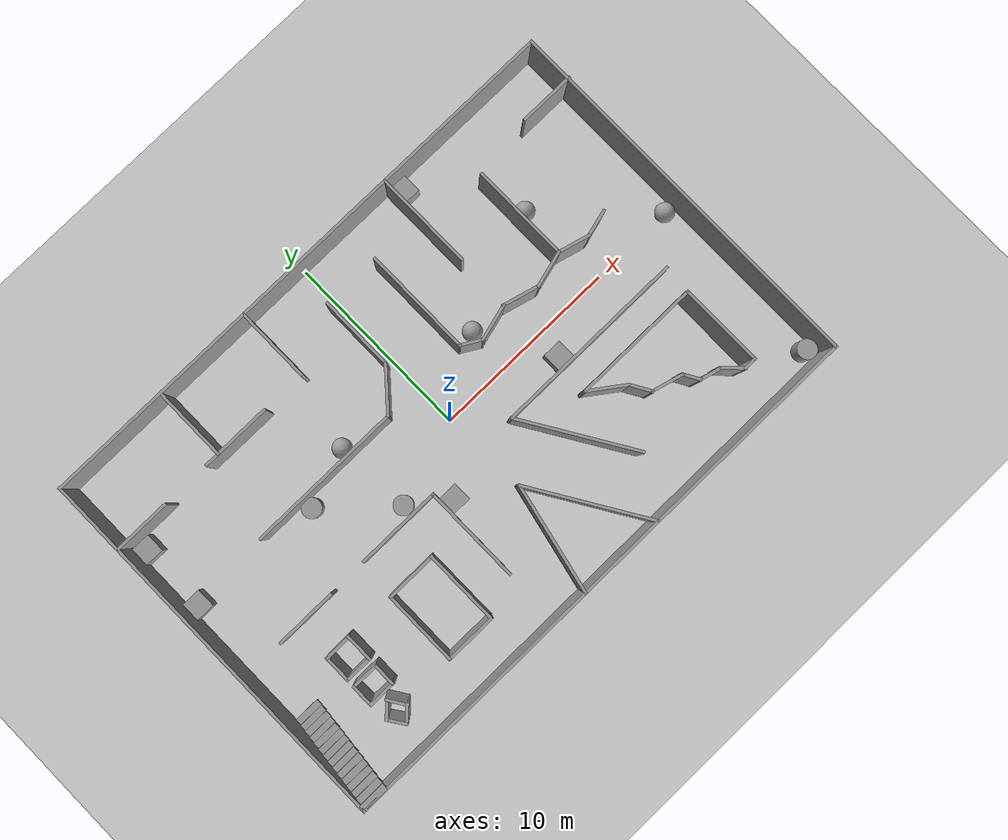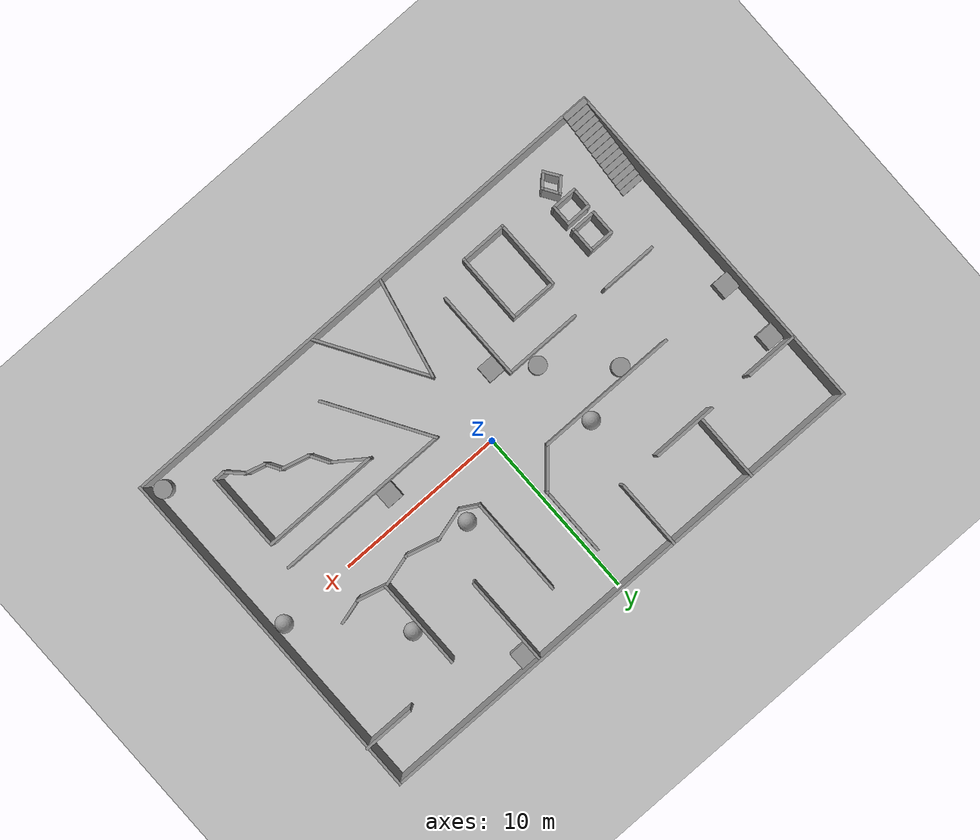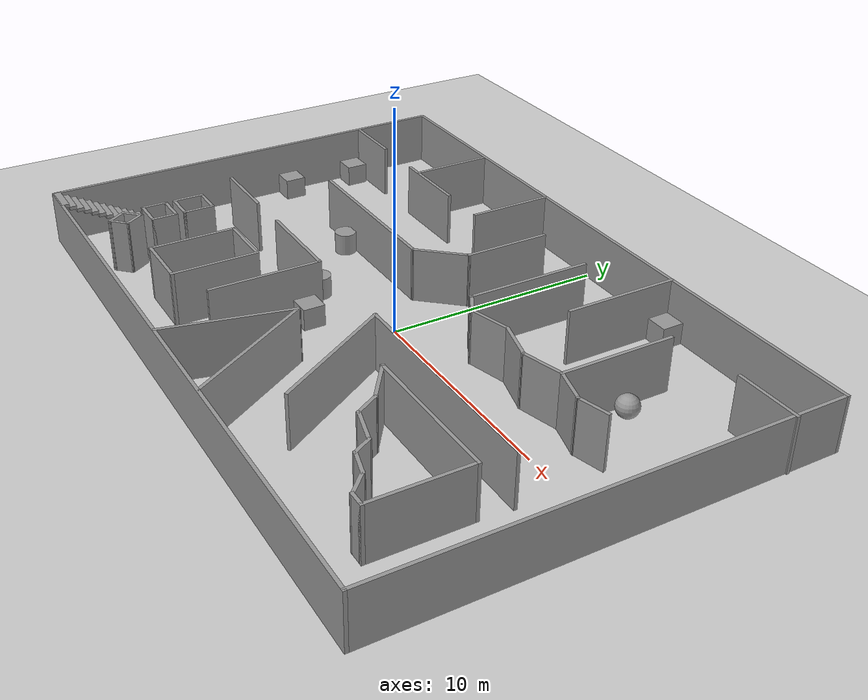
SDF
<sdf version="1.7">
 <world name="default">
  <light name="sun" type="directional">
   <pose>0 0 10 0 -0 0</pose>
   <diffuse>0.8 0.8 0.8 1</diffuse>
   <specular>0.2 0.2 0.2 1</specular>
   <attenuation>
    <range>1000</range>
    <constant>0.9</constant>
    <linear>0.01</linear>
    <quadratic>0.001</quadratic>
   </attenuation>
   <direction>-0.5 0.1 -0.9</direction>
   <spot><inner_angle>0</inner_angle><outer_angle>0</outer_angle><falloff>0</falloff></spot>
  </light>
  <model name="ground_plane">
   <static>1</static>
   <link name="link">
    <collision name="collision">
     <geometry><plane><normal>0 0 1</normal><size>100 100</size></plane></geometry>
     <surface>
      <contact><collide_bitmask>65535</collide_bitmask></contact>
      <friction><ode><mu>100</mu><mu2>50</mu2></ode></friction>
     </surface>
    </collision>
    <visual name="visual">
     <cast_shadows>0</cast_shadows>
     <geometry><plane><normal>0 0 1</normal><size>100 100</size></plane></geometry>
     <material>
      <script><uri>file://media/materials/scripts/gazebo.material</uri><name>Gazebo/Grey</name></script>
     </material>
    </visual>
   </link>
  </model>
  <gravity>0 0 -9.8</gravity>
  <magnetic_field>6e-06 2.3e-05 -4.2e-05</magnetic_field>
  <atmosphere type="adiabatic"/>
  <physics name="default_physics" default="0" type="ode">
   <max_step_size>0.001</max_step_size>
   <real_time_factor>1</real_time_factor>
   <real_time_update_rate>1000</real_time_update_rate>
  </physics>
  <scene><ambient>0.4 0.4 0.4 1</ambient><background>0.7 0.7 0.7 1</background><shadows>1</shadows></scene>
  <audio><device>default</device></audio>
  <spherical_coordinates>
   <surface_model>EARTH_WGS84</surface_model>
   <latitude_deg>0</latitude_deg>
   <longitude_deg>0</longitude_deg>
   <elevation>0</elevation>
   <heading_deg>0</heading_deg>
  </spherical_coordinates>
  <model name="unit_box">
   <pose>-14.3506 5.42319 0.5 0 -0 0</pose>
   <link name="link">
    <inertial>
     <mass>1</mass>
     <inertia>
      <ixx>0.166667</ixx>
      <ixy>0</ixy>
      <ixz>0</ixz>
      <iyy>0.166667</iyy>
      <iyz>0</iyz>
      <izz>0.166667</izz>
     </inertia>
    </inertial>
    <collision name="collision"><geometry><box><size>1 1 1</size></box></geometry></collision>
    <visual name="visual">
     <geometry><box><size>1 1 1</size></box></geometry>
     <material>
      <script><name>Gazebo/Grey</name><uri>file://media/materials/scripts/gazebo.material</uri></script>
     </material>
    </visual>
   </link>
  </model>
  <model name="unit_sphere">
   <pose>14.3692 0.007494 0.5 0 -0 0</pose>
   <link name="link">
    <inertial>
     <mass>1</mass>
     <inertia><ixx>0.1</ixx><ixy>0</ixy><ixz>0</ixz><iyy>0.1</iyy><iyz>0</iyz><izz>0.1</izz></inertia>
    </inertial>
    <collision name="collision"><geometry><sphere><radius>0.5</radius></sphere></geometry></collision>
    <visual name="visual">
     <geometry><sphere><radius>0.5</radius></sphere></geometry>
     <material>
      <script><name>Gazebo/Grey</name><uri>file://media/materials/scripts/gazebo.material</uri></script>
     </material>
    </visual>
   </link>
  </model>
  <model name="Untitled_0">
   <link name="Stairs_0">
    <visual name="Stairs_0_Visual_0">
     <pose>-14.3145 -5.2358 0.083333 0 -0 0</pose>
     <geometry><box><size>1.45112 0.330096 0.166667</size></box></geometry>
     <material>
      <script><uri>file://media/materials/scripts/gazebo.material</uri><name>Gazebo/Grey</name></script>
      <ambient>1 1 1 1</ambient>
      <shader type="pixel"/>
     </material>
     <meta><layer>0</layer></meta>
    </visual>
    <visual name="Stairs_0_Visual_1">
     <pose>-14.3145 -5.5659 0.25 0 -0 0</pose>
     <geometry><box><size>1.45112 0.330096 0.166667</size></box></geometry>
     <material>
      <script><uri>file://media/materials/scripts/gazebo.material</uri><name>Gazebo/Grey</name></script>
      <ambient>1 1 1 1</ambient>
      <shader type="pixel"/>
     </material>
     <meta><layer>0</layer></meta>
    </visual>
    <visual name="Stairs_0_Visual_2">
     <pose>-14.3145 -5.89599 0.416667 0 -0 0</pose>
     <geometry><box><size>1.45112 0.330096 0.166667</size></box></geometry>
     <material>
      <script><uri>file://media/materials/scripts/gazebo.material</uri><name>Gazebo/Grey</name></script>
      <ambient>1 1 1 1</ambient>
      <shader type="pixel"/>
     </material>
     <meta><layer>0</layer></meta>
    </visual>
    <visual name="Stairs_0_Visual_3">
     <pose>-14.3145 -6.22609 0.583333 0 -0 0</pose>
     <geometry><box><size>1.45112 0.330096 0.166667</size></box></geometry>
     <material>
      <script><uri>file://media/materials/scripts/gazebo.material</uri><name>Gazebo/Grey</name></script>
      <ambient>1 1 1 1</ambient>
      <shader type="pixel"/>
     </material>
     <meta><layer>0</layer></meta>
    </visual>
    <visual name="Stairs_0_Visual_4">
     <pose>-14.3145 -6.55619 0.75 0 -0 0</pose>
     <geometry><box><size>1.45112 0.330096 0.166667</size></box></geometry>
     <material>
      <script><uri>file://media/materials/scripts/gazebo.material</uri><name>Gazebo/Grey</name></script>
      <ambient>1 1 1 1</ambient>
      <shader type="pixel"/>
     </material>
     <meta><layer>0</layer></meta>
    </visual>
    <visual name="Stairs_0_Visual_5">
     <pose>-14.3145 -6.88628 0.916667 0 -0 0</pose>
     <geometry><box><size>1.45112 0.330096 0.166667</size></box></geometry>
     <material>
      <script><uri>file://media/materials/scripts/gazebo.material</uri><name>Gazebo/Grey</name></script>
      <ambient>1 1 1 1</ambient>
      <shader type="pixel"/>
     </material>
     <meta><layer>0</layer></meta>
    </visual>
    <visual name="Stairs_0_Visual_6">
     <pose>-14.3145 -7.21638 1.08333 0 -0 0</pose>
     <geometry><box><size>1.45112 0.330096 0.166667</size></box></geometry>
     <material>
      <script><uri>file://media/materials/scripts/gazebo.material</uri><name>Gazebo/Grey</name></script>
      <ambient>1 1 1 1</ambient>
      <shader type="pixel"/>
     </material>
     <meta><layer>0</layer></meta>
    </visual>
    <visual name="Stairs_0_Visual_7">
     <pose>-14.3145 -7.54648 1.25 0 -0 0</pose>
     <geometry><box><size>1.45112 0.330096 0.166667</size></box></geometry>
     <material>
      <script><uri>file://media/materials/scripts/gazebo.material</uri><name>Gazebo/Grey</name></script>
      <ambient>1 1 1 1</ambient>
      <shader type="pixel"/>
     </material>
     <meta><layer>0</layer></meta>
    </visual>
    <visual name="Stairs_0_Visual_8">
     <pose>-14.3145 -7.87657 1.41667 0 -0 0</pose>
     <geometry><box><size>1.45112 0.330096 0.166667</size></box></geometry>
     <material>
      <script><uri>file://media/materials/scripts/gazebo.material</uri><name>Gazebo/Grey</name></script>
      <ambient>1 1 1 1</ambient>
      <shader type="pixel"/>
     </material>
     <meta><layer>0</layer></meta>
    </visual>
    <visual name="Stairs_0_Visual_9">
     <pose>-14.3145 -8.20667 1.58333 0 -0 0</pose>
     <geometry><box><size>1.45112 0.330096 0.166667</size></box></geometry>
     <material>
      <script><uri>file://media/materials/scripts/gazebo.material</uri><name>Gazebo/Grey</name></script>
      <ambient>1 1 1 1</ambient>
      <shader type="pixel"/>
     </material>
     <meta><layer>0</layer></meta>
    </visual>
    <visual name="Stairs_0_Visual_10">
     <pose>-14.3145 -8.53676 1.75 0 -0 0</pose>
     <geometry><box><size>1.45112 0.330096 0.166667</size></box></geometry>
     <material>
      <script><uri>file://media/materials/scripts/gazebo.material</uri><name>Gazebo/Grey</name></script>
      <ambient>1 1 1 1</ambient>
      <shader type="pixel"/>
     </material>
     <meta><layer>0</layer></meta>
    </visual>
    <visual name="Stairs_0_Visual_11">
     <pose>-14.3145 -8.86686 1.91667 0 -0 0</pose>
     <geometry><box><size>1.45112 0.330096 0.166667</size></box></geometry>
     <material>
      <script><uri>file://media/materials/scripts/gazebo.material</uri><name>Gazebo/Grey</name></script>
      <ambient>1 1 1 1</ambient>
      <shader type="pixel"/>
     </material>
     <meta><layer>0</layer></meta>
    </visual>
    <visual name="Stairs_0_Visual_12">
     <pose>-14.3145 -9.19696 2.08333 0 -0 0</pose>
     <geometry><box><size>1.45112 0.330096 0.166667</size></box></geometry>
     <material>
      <script><uri>file://media/materials/scripts/gazebo.material</uri><name>Gazebo/Grey</name></script>
      <ambient>1 1 1 1</ambient>
      <shader type="pixel"/>
     </material>
     <meta><layer>0</layer></meta>
    </visual>
    <visual name="Stairs_0_Visual_13">
     <pose>-14.3145 -9.52705 2.25 0 -0 0</pose>
     <geometry><box><size>1.45112 0.330096 0.166667</size></box></geometry>
     <material>
      <script><uri>file://media/materials/scripts/gazebo.material</uri><name>Gazebo/Grey</name></script>
      <ambient>1 1 1 1</ambient>
      <shader type="pixel"/>
     </material>
     <meta><layer>0</layer></meta>
    </visual>
    <visual name="Stairs_0_Visual_14">
     <pose>-14.3145 -9.85715 2.41667 0 -0 0</pose>
     <geometry><box><size>1.45112 0.330096 0.166667</size></box></geometry>
     <material>
      <script><uri>file://media/materials/scripts/gazebo.material</uri><name>Gazebo/Grey</name></script>
      <ambient>1 1 1 1</ambient>
      <shader type="pixel"/>
     </material>
     <meta><layer>0</layer></meta>
    </visual>
    <collision name="Stairs_0_Collision_0">
     <pose>-14.3145 -5.2358 0.083333 0 -0 0</pose>
     <geometry><box><size>1.45112 0.330096 0.166667</size></box></geometry>
     <surface>
      <friction>
       <ode><mu>1</mu><mu2>1</mu2><fdir1>0 0 0</fdir1><slip1>0</slip1><slip2>0</slip2></ode>
       <torsional>
        <coefficient>1</coefficient>
        <patch_radius>0</patch_radius>
        <surface_radius>0</surface_radius>
        <use_patch_radius>1</use_patch_radius>
        <ode><slip>0</slip></ode>
       </torsional>
      </friction>
      <bounce><restitution_coefficient>0</restitution_coefficient><threshold>1e+06</threshold></bounce>
      <contact>
       <collide_without_contact>0</collide_without_contact>
       <collide_without_contact_bitmask>1</collide_without_contact_bitmask>
       <collide_bitmask>1</collide_bitmask>
       <ode>
        <soft_cfm>0</soft_cfm>
        <soft_erp>0.2</soft_erp>
        <kp>1e+13</kp>
        <kd>1</kd>
        <max_vel>0.01</max_vel>
        <min_depth>0</min_depth>
       </ode>
       <bullet>
        <split_impulse>1</split_impulse>
        <split_impulse_penetration_threshold>-0.01</split_impulse_penetration_threshold>
        <soft_cfm>0</soft_cfm>
        <soft_erp>0.2</soft_erp>
        <kp>1e+13</kp>
        <kd>1</kd>
       </bullet>
      </contact>
     </surface>
    </collision>
    <collision name="Stairs_0_Collision_1">
     <pose>-14.3145 -5.5659 0.25 0 -0 0</pose>
     <geometry><box><size>1.45112 0.330096 0.166667</size></box></geometry>
     <surface>
      <friction>
       <ode><mu>1</mu><mu2>1</mu2><fdir1>0 0 0</fdir1><slip1>0</slip1><slip2>0</slip2></ode>
       <torsional>
        <coefficient>1</coefficient>
        <patch_radius>0</patch_radius>
        <surface_radius>0</surface_radius>
        <use_patch_radius>1</use_patch_radius>
        <ode><slip>0</slip></ode>
       </torsional>
      </friction>
      <bounce><restitution_coefficient>0</restitution_coefficient><threshold>1e+06</threshold></bounce>
      <contact>
       <collide_without_contact>0</collide_without_contact>
       <collide_without_contact_bitmask>1</collide_without_contact_bitmask>
       <collide_bitmask>1</collide_bitmask>
       <ode>
        <soft_cfm>0</soft_cfm>
        <soft_erp>0.2</soft_erp>
        <kp>1e+13</kp>
        <kd>1</kd>
        <max_vel>0.01</max_vel>
        <min_depth>0</min_depth>
       </ode>
       <bullet>
        <split_impulse>1</split_impulse>
        <split_impulse_penetration_threshold>-0.01</split_impulse_penetration_threshold>
        <soft_cfm>0</soft_cfm>
        <soft_erp>0.2</soft_erp>
        <kp>1e+13</kp>
        <kd>1</kd>
       </bullet>
      </contact>
     </surface>
    </collision>
    <collision name="Stairs_0_Collision_2">
     <pose>-14.3145 -5.89599 0.416667 0 -0 0</pose>
     <geometry><box><size>1.45112 0.330096 0.166667</size></box></geometry>
     <surface>
      <friction>
       <ode><mu>1</mu><mu2>1</mu2><fdir1>0 0 0</fdir1><slip1>0</slip1><slip2>0</slip2></ode>
       <torsional>
        <coefficient>1</coefficient>
        <patch_radius>0</patch_radius>
        <surface_radius>0</surface_radius>
        <use_patch_radius>1</use_patch_radius>
        <ode><slip>0</slip></ode>
       </torsional>
      </friction>
      <bounce><restitution_coefficient>0</restitution_coefficient><threshold>1e+06</threshold></bounce>
      <contact>
       <collide_without_contact>0</collide_without_contact>
       <collide_without_contact_bitmask>1</collide_without_contact_bitmask>
       <collide_bitmask>1</collide_bitmask>
       <ode>
        <soft_cfm>0</soft_cfm>
        <soft_erp>0.2</soft_erp>
        <kp>1e+13</kp>
        <kd>1</kd>
        <max_vel>0.01</max_vel>
        <min_depth>0</min_depth>
       </ode>
       <bullet>
        <split_impulse>1</split_impulse>
        <split_impulse_penetration_threshold>-0.01</split_impulse_penetration_threshold>
        <soft_cfm>0</soft_cfm>
        <soft_erp>0.2</soft_erp>
        <kp>1e+13</kp>
        <kd>1</kd>
       </bullet>
      </contact>
     </surface>
    </collision>
    <collision name="Stairs_0_Collision_4">
     <pose>-14.3145 -6.55619 0.75 0 -0 0</pose>
     <geometry><box><size>1.45112 0.330096 0.166667</size></box></geometry>
     <surface>
      <friction>
       <ode><mu>1</mu><mu2>1</mu2><fdir1>0 0 0</fdir1><slip1>0</slip1><slip2>0</slip2></ode>
       <torsional>
        <coefficient>1</coefficient>
        <patch_radius>0</patch_radius>
        <surface_radius>0</surface_radius>
        <use_patch_radius>1</use_patch_radius>
        <ode><slip>0</slip></ode>
       </torsional>
      </friction>
      <bounce><restitution_coefficient>0</restitution_coefficient><threshold>1e+06</threshold></bounce>
      <contact>
       <collide_without_contact>0</collide_without_contact>
       <collide_without_contact_bitmask>1</collide_without_contact_bitmask>
       <collide_bitmask>1</collide_bitmask>
       <ode>
        <soft_cfm>0</soft_cfm>
        <soft_erp>0.2</soft_erp>
        <kp>1e+13</kp>
        <kd>1</kd>
        <max_vel>0.01</max_vel>
        <min_depth>0</min_depth>
       </ode>
       <bullet>
        <split_impulse>1</split_impulse>
        <split_impulse_penetration_threshold>-0.01</split_impulse_penetration_threshold>
        <soft_cfm>0</soft_cfm>
        <soft_erp>0.2</soft_erp>
        <kp>1e+13</kp>
        <kd>1</kd>
       </bullet>
      </contact>
     </surface>
    </collision>
    <collision name="Stairs_0_Collision_3">
     <pose>-14.3145 -6.22609 0.583333 0 -0 0</pose>
     <geometry><box><size>1.45112 0.330096 0.166667</size></box></geometry>
     <surface>
      <friction>
       <ode><mu>1</mu><mu2>1</mu2><fdir1>0 0 0</fdir1><slip1>0</slip1><slip2>0</slip2></ode>
       <torsional>
        <coefficient>1</coefficient>
        <patch_radius>0</patch_radius>
        <surface_radius>0</surface_radius>
        <use_patch_radius>1</use_patch_radius>
        <ode><slip>0</slip></ode>
       </torsional>
      </friction>
      <bounce><restitution_coefficient>0</restitution_coefficient><threshold>1e+06</threshold></bounce>
      <contact>
       <collide_without_contact>0</collide_without_contact>
       <collide_without_contact_bitmask>1</collide_without_contact_bitmask>
       <collide_bitmask>1</collide_bitmask>
       <ode>
        <soft_cfm>0</soft_cfm>
        <soft_erp>0.2</soft_erp>
        <kp>1e+13</kp>
        <kd>1</kd>
        <max_vel>0.01</max_vel>
        <min_depth>0</min_depth>
       </ode>
       <bullet>
        <split_impulse>1</split_impulse>
        <split_impulse_penetration_threshold>-0.01</split_impulse_penetration_threshold>
        <soft_cfm>0</soft_cfm>
        <soft_erp>0.2</soft_erp>
        <kp>1e+13</kp>
        <kd>1</kd>
       </bullet>
      </contact>
     </surface>
    </collision>
    <collision name="Stairs_0_Collision_5">
     <pose>-14.3145 -6.88628 0.916667 0 -0 0</pose>
     <geometry><box><size>1.45112 0.330096 0.166667</size></box></geometry>
     <surface>
      <friction>
       <ode><mu>1</mu><mu2>1</mu2><fdir1>0 0 0</fdir1><slip1>0</slip1><slip2>0</slip2></ode>
       <torsional>
        <coefficient>1</coefficient>
        <patch_radius>0</patch_radius>
        <surface_radius>0</surface_radius>
        <use_patch_radius>1</use_patch_radius>
        <ode><slip>0</slip></ode>
       </torsional>
      </friction>
      <bounce><restitution_coefficient>0</restitution_coefficient><threshold>1e+06</threshold></bounce>
      <contact>
       <collide_without_contact>0</collide_without_contact>
       <collide_without_contact_bitmask>1</collide_without_contact_bitmask>
       <collide_bitmask>1</collide_bitmask>
       <ode>
        <soft_cfm>0</soft_cfm>
        <soft_erp>0.2</soft_erp>
        <kp>1e+13</kp>
        <kd>1</kd>
        <max_vel>0.01</max_vel>
        <min_depth>0</min_depth>
       </ode>
       <bullet>
        <split_impulse>1</split_impulse>
        <split_impulse_penetration_threshold>-0.01</split_impulse_penetration_threshold>
        <soft_cfm>0</soft_cfm>
        <soft_erp>0.2</soft_erp>
        <kp>1e+13</kp>
        <kd>1</kd>
       </bullet>
      </contact>
     </surface>
    </collision>
    <collision name="Stairs_0_Collision_6">
     <pose>-14.3145 -7.21638 1.08333 0 -0 0</pose>
     <geometry><box><size>1.45112 0.330096 0.166667</size></box></geometry>
     <surface>
      <friction>
       <ode><mu>1</mu><mu2>1</mu2><fdir1>0 0 0</fdir1><slip1>0</slip1><slip2>0</slip2></ode>
       <torsional>
        <coefficient>1</coefficient>
        <patch_radius>0</patch_radius>
        <surface_radius>0</surface_radius>
        <use_patch_radius>1</use_patch_radius>
        <ode><slip>0</slip></ode>
       </torsional>
      </friction>
      <bounce><restitution_coefficient>0</restitution_coefficient><threshold>1e+06</threshold></bounce>
      <contact>
       <collide_without_contact>0</collide_without_contact>
       <collide_without_contact_bitmask>1</collide_without_contact_bitmask>
       <collide_bitmask>1</collide_bitmask>
       <ode>
        <soft_cfm>0</soft_cfm>
        <soft_erp>0.2</soft_erp>
        <kp>1e+13</kp>
        <kd>1</kd>
        <max_vel>0.01</max_vel>
        <min_depth>0</min_depth>
       </ode>
       <bullet>
        <split_impulse>1</split_impulse>
        <split_impulse_penetration_threshold>-0.01</split_impulse_penetration_threshold>
        <soft_cfm>0</soft_cfm>
        <soft_erp>0.2</soft_erp>
        <kp>1e+13</kp>
        <kd>1</kd>
       </bullet>
      </contact>
     </surface>
    </collision>
    <collision name="Stairs_0_Collision_7">
     <pose>-14.3145 -7.54648 1.25 0 -0 0</pose>
     <geometry><box><size>1.45112 0.330096 0.166667</size></box></geometry>
     <surface>
      <friction>
       <ode><mu>1</mu><mu2>1</mu2><fdir1>0 0 0</fdir1><slip1>0</slip1><slip2>0</slip2></ode>
       <torsional>
        <coefficient>1</coefficient>
        <patch_radius>0</patch_radius>
        <surface_radius>0</surface_radius>
        <use_patch_radius>1</use_patch_radius>
        <ode><slip>0</slip></ode>
       </torsional>
      </friction>
      <bounce><restitution_coefficient>0</restitution_coefficient><threshold>1e+06</threshold></bounce>
      <contact>
       <collide_without_contact>0</collide_without_contact>
       <collide_without_contact_bitmask>1</collide_without_contact_bitmask>
       <collide_bitmask>1</collide_bitmask>
       <ode>
        <soft_cfm>0</soft_cfm>
        <soft_erp>0.2</soft_erp>
        <kp>1e+13</kp>
        <kd>1</kd>
        <max_vel>0.01</max_vel>
        <min_depth>0</min_depth>
       </ode>
       <bullet>
        <split_impulse>1</split_impulse>
        <split_impulse_penetration_threshold>-0.01</split_impulse_penetration_threshold>
        <soft_cfm>0</soft_cfm>
        <soft_erp>0.2</soft_erp>
        <kp>1e+13</kp>
        <kd>1</kd>
       </bullet>
      </contact>
     </surface>
    </collision>
    <collision name="Stairs_0_Collision_8">
     <pose>-14.3145 -7.87657 1.41667 0 -0 0</pose>
     <geometry><box><size>1.45112 0.330096 0.166667</size></box></geometry>
     <surface>
      <friction>
       <ode><mu>1</mu><mu2>1</mu2><fdir1>0 0 0</fdir1><slip1>0</slip1><slip2>0</slip2></ode>
       <torsional>
        <coefficient>1</coefficient>
        <patch_radius>0</patch_radius>
        <surface_radius>0</surface_radius>
        <use_patch_radius>1</use_patch_radius>
        <ode><slip>0</slip></ode>
       </torsional>
      </friction>
      <bounce><restitution_coefficient>0</restitution_coefficient><threshold>1e+06</threshold></bounce>
      <contact>
       <collide_without_contact>0</collide_without_contact>
       <collide_without_contact_bitmask>1</collide_without_contact_bitmask>
       <collide_bitmask>1</collide_bitmask>
       <ode>
        <soft_cfm>0</soft_cfm>
        <soft_erp>0.2</soft_erp>
        <kp>1e+13</kp>
        <kd>1</kd>
        <max_vel>0.01</max_vel>
        <min_depth>0</min_depth>
       </ode>
       <bullet>
        <split_impulse>1</split_impulse>
        <split_impulse_penetration_threshold>-0.01</split_impulse_penetration_threshold>
        <soft_cfm>0</soft_cfm>
        <soft_erp>0.2</soft_erp>
        <kp>1e+13</kp>
        <kd>1</kd>
       </bullet>
      </contact>
     </surface>
    </collision>
    <collision name="Stairs_0_Collision_9">
     <pose>-14.3145 -8.20667 1.58333 0 -0 0</pose>
     <geometry><box><size>1.45112 0.330096 0.166667</size></box></geometry>
     <surface>
      <friction>
       <ode><mu>1</mu><mu2>1</mu2><fdir1>0 0 0</fdir1><slip1>0</slip1><slip2>0</slip2></ode>
       <torsional>
        <coefficient>1</coefficient>
        <patch_radius>0</patch_radius>
        <surface_radius>0</surface_radius>
        <use_patch_radius>1</use_patch_radius>
        <ode><slip>0</slip></ode>
       </torsional>
      </friction>
      <bounce><restitution_coefficient>0</restitution_coefficient><threshold>1e+06</threshold></bounce>
      <contact>
       <collide_without_contact>0</collide_without_contact>
       <collide_without_contact_bitmask>1</collide_without_contact_bitmask>
       <collide_bitmask>1</collide_bitmask>
       <ode>
        <soft_cfm>0</soft_cfm>
        <soft_erp>0.2</soft_erp>
        <kp>1e+13</kp>
        <kd>1</kd>
        <max_vel>0.01</max_vel>
        <min_depth>0</min_depth>
       </ode>
       <bullet>
        <split_impulse>1</split_impulse>
        <split_impulse_penetration_threshold>-0.01</split_impulse_penetration_threshold>
        <soft_cfm>0</soft_cfm>
        <soft_erp>0.2</soft_erp>
        <kp>1e+13</kp>
        <kd>1</kd>
       </bullet>
      </contact>
     </surface>
    </collision>
    <collision name="Stairs_0_Collision_10">
     <pose>-14.3145 -8.53676 1.75 0 -0 0</pose>
     <geometry><box><size>1.45112 0.330096 0.166667</size></box></geometry>
     <surface>
      <friction>
       <ode><mu>1</mu><mu2>1</mu2><fdir1>0 0 0</fdir1><slip1>0</slip1><slip2>0</slip2></ode>
       <torsional>
        <coefficient>1</coefficient>
        <patch_radius>0</patch_radius>
        <surface_radius>0</surface_radius>
        <use_patch_radius>1</use_patch_radius>
        <ode><slip>0</slip></ode>
       </torsional>
      </friction>
      <bounce><restitution_coefficient>0</restitution_coefficient><threshold>1e+06</threshold></bounce>
      <contact>
       <collide_without_contact>0</collide_without_contact>
       <collide_without_contact_bitmask>1</collide_without_contact_bitmask>
       <collide_bitmask>1</collide_bitmask>
       <ode>
        <soft_cfm>0</soft_cfm>
        <soft_erp>0.2</soft_erp>
        <kp>1e+13</kp>
        <kd>1</kd>
        <max_vel>0.01</max_vel>
        <min_depth>0</min_depth>
       </ode>
       <bullet>
        <split_impulse>1</split_impulse>
        <split_impulse_penetration_threshold>-0.01</split_impulse_penetration_threshold>
        <soft_cfm>0</soft_cfm>
        <soft_erp>0.2</soft_erp>
        <kp>1e+13</kp>
        <kd>1</kd>
       </bullet>
      </contact>
     </surface>
    </collision>
    <collision name="Stairs_0_Collision_12">
     <pose>-14.3145 -9.19696 2.08333 0 -0 0</pose>
     <geometry><box><size>1.45112 0.330096 0.166667</size></box></geometry>
     <surface>
      <friction>
       <ode><mu>1</mu><mu2>1</mu2><fdir1>0 0 0</fdir1><slip1>0</slip1><slip2>0</slip2></ode>
       <torsional>
        <coefficient>1</coefficient>
        <patch_radius>0</patch_radius>
        <surface_radius>0</surface_radius>
        <use_patch_radius>1</use_patch_radius>
        <ode><slip>0</slip></ode>
       </torsional>
      </friction>
      <bounce><restitution_coefficient>0</restitution_coefficient><threshold>1e+06</threshold></bounce>
      <contact>
       <collide_without_contact>0</collide_without_contact>
       <collide_without_contact_bitmask>1</collide_without_contact_bitmask>
       <collide_bitmask>1</collide_bitmask>
       <ode>
        <soft_cfm>0</soft_cfm>
        <soft_erp>0.2</soft_erp>
        <kp>1e+13</kp>
        <kd>1</kd>
        <max_vel>0.01</max_vel>
        <min_depth>0</min_depth>
       </ode>
       <bullet>
        <split_impulse>1</split_impulse>
        <split_impulse_penetration_threshold>-0.01</split_impulse_penetration_threshold>
        <soft_cfm>0</soft_cfm>
        <soft_erp>0.2</soft_erp>
        <kp>1e+13</kp>
        <kd>1</kd>
       </bullet>
      </contact>
     </surface>
    </collision>
    <collision name="Stairs_0_Collision_11">
     <pose>-14.3145 -8.86686 1.91667 0 -0 0</pose>
     <geometry><box><size>1.45112 0.330096 0.166667</size></box></geometry>
     <surface>
      <friction>
       <ode><mu>1</mu><mu2>1</mu2><fdir1>0 0 0</fdir1><slip1>0</slip1><slip2>0</slip2></ode>
       <torsional>
        <coefficient>1</coefficient>
        <patch_radius>0</patch_radius>
        <surface_radius>0</surface_radius>
        <use_patch_radius>1</use_patch_radius>
        <ode><slip>0</slip></ode>
       </torsional>
      </friction>
      <bounce><restitution_coefficient>0</restitution_coefficient><threshold>1e+06</threshold></bounce>
      <contact>
       <collide_without_contact>0</collide_without_contact>
       <collide_without_contact_bitmask>1</collide_without_contact_bitmask>
       <collide_bitmask>1</collide_bitmask>
       <ode>
        <soft_cfm>0</soft_cfm>
        <soft_erp>0.2</soft_erp>
        <kp>1e+13</kp>
        <kd>1</kd>
        <max_vel>0.01</max_vel>
        <min_depth>0</min_depth>
       </ode>
       <bullet>
        <split_impulse>1</split_impulse>
        <split_impulse_penetration_threshold>-0.01</split_impulse_penetration_threshold>
        <soft_cfm>0</soft_cfm>
        <soft_erp>0.2</soft_erp>
        <kp>1e+13</kp>
        <kd>1</kd>
       </bullet>
      </contact>
     </surface>
    </collision>
    <collision name="Stairs_0_Collision_13">
     <pose>-14.3145 -9.52705 2.25 0 -0 0</pose>
     <geometry><box><size>1.45112 0.330096 0.166667</size></box></geometry>
     <surface>
      <friction>
       <ode><mu>1</mu><mu2>1</mu2><fdir1>0 0 0</fdir1><slip1>0</slip1><slip2>0</slip2></ode>
       <torsional>
        <coefficient>1</coefficient>
        <patch_radius>0</patch_radius>
        <surface_radius>0</surface_radius>
        <use_patch_radius>1</use_patch_radius>
        <ode><slip>0</slip></ode>
       </torsional>
      </friction>
      <bounce><restitution_coefficient>0</restitution_coefficient><threshold>1e+06</threshold></bounce>
      <contact>
       <collide_without_contact>0</collide_without_contact>
       <collide_without_contact_bitmask>1</collide_without_contact_bitmask>
       <collide_bitmask>1</collide_bitmask>
       <ode>
        <soft_cfm>0</soft_cfm>
        <soft_erp>0.2</soft_erp>
        <kp>1e+13</kp>
        <kd>1</kd>
        <max_vel>0.01</max_vel>
        <min_depth>0</min_depth>
       </ode>
       <bullet>
        <split_impulse>1</split_impulse>
        <split_impulse_penetration_threshold>-0.01</split_impulse_penetration_threshold>
        <soft_cfm>0</soft_cfm>
        <soft_erp>0.2</soft_erp>
        <kp>1e+13</kp>
        <kd>1</kd>
       </bullet>
      </contact>
     </surface>
    </collision>
    <collision name="Stairs_0_Collision_14">
     <pose>-14.3145 -9.85715 2.41667 0 -0 0</pose>
     <geometry><box><size>1.45112 0.330096 0.166667</size></box></geometry>
     <surface>
      <friction>
       <ode><mu>1</mu><mu2>1</mu2><fdir1>0 0 0</fdir1><slip1>0</slip1><slip2>0</slip2></ode>
       <torsional>
        <coefficient>1</coefficient>
        <patch_radius>0</patch_radius>
        <surface_radius>0</surface_radius>
        <use_patch_radius>1</use_patch_radius>
        <ode><slip>0</slip></ode>
       </torsional>
      </friction>
      <bounce><restitution_coefficient>0</restitution_coefficient><threshold>1e+06</threshold></bounce>
      <contact>
       <collide_without_contact>0</collide_without_contact>
       <collide_without_contact_bitmask>1</collide_without_contact_bitmask>
       <collide_bitmask>1</collide_bitmask>
       <ode>
        <soft_cfm>0</soft_cfm>
        <soft_erp>0.2</soft_erp>
        <kp>1e+13</kp>
        <kd>1</kd>
        <max_vel>0.01</max_vel>
        <min_depth>0</min_depth>
       </ode>
       <bullet>
        <split_impulse>1</split_impulse>
        <split_impulse_penetration_threshold>-0.01</split_impulse_penetration_threshold>
        <soft_cfm>0</soft_cfm>
        <soft_erp>0.2</soft_erp>
        <kp>1e+13</kp>
        <kd>1</kd>
       </bullet>
      </contact>
     </surface>
    </collision>
   </link>
   <link name="Wall_101">
    <pose>8.911 4.53478 0 0 -0 1.5708</pose>
    <visual name="Wall_101_Visual">
     <pose>0 0 1.25 0 -0 0</pose>
     <geometry><box><size>5.25 0.15 2.5</size></box></geometry>
     <material>
      <script><uri>file://media/materials/scripts/gazebo.material</uri><name>Gazebo/Grey</name></script>
      <ambient>1 1 1 1</ambient>
      <shader type="pixel"/>
     </material>
     <meta><layer>0</layer></meta>
    </visual>
    <collision name="Wall_101_Collision">
     <pose>0 0 1.25 0 -0 0</pose>
     <geometry><box><size>5.25 0.15 2.5</size></box></geometry>
     <surface>
      <friction>
       <ode><mu>1</mu><mu2>1</mu2><fdir1>0 0 0</fdir1><slip1>0</slip1><slip2>0</slip2></ode>
       <torsional>
        <coefficient>1</coefficient>
        <patch_radius>0</patch_radius>
        <surface_radius>0</surface_radius>
        <use_patch_radius>1</use_patch_radius>
        <ode><slip>0</slip></ode>
       </torsional>
      </friction>
      <bounce><restitution_coefficient>0</restitution_coefficient><threshold>1e+06</threshold></bounce>
      <contact>
       <collide_without_contact>0</collide_without_contact>
       <collide_without_contact_bitmask>1</collide_without_contact_bitmask>
       <collide_bitmask>1</collide_bitmask>
       <ode>
        <soft_cfm>0</soft_cfm>
        <soft_erp>0.2</soft_erp>
        <kp>1e+13</kp>
        <kd>1</kd>
        <max_vel>0.01</max_vel>
        <min_depth>0</min_depth>
       </ode>
       <bullet>
        <split_impulse>1</split_impulse>
        <split_impulse_penetration_threshold>-0.01</split_impulse_penetration_threshold>
        <soft_cfm>0</soft_cfm>
        <soft_erp>0.2</soft_erp>
        <kp>1e+13</kp>
        <kd>1</kd>
       </bullet>
      </contact>
     </surface>
    </collision>
   </link>
   <link name="Wall_105">
    <pose>13.6032 7.54437 0 0 -0 3.14159</pose>
    <visual name="Wall_105_Visual">
     <pose>0 0 1.25 0 -0 0</pose>
     <geometry><box><size>3 0.15 2.5</size></box></geometry>
     <material>
      <script><uri>file://media/materials/scripts/gazebo.material</uri><name>Gazebo/Grey</name></script>
      <ambient>1 1 1 1</ambient>
      <shader type="pixel"/>
     </material>
     <meta><layer>0</layer></meta>
    </visual>
    <collision name="Wall_105_Collision">
     <pose>0 0 1.25 0 -0 0</pose>
     <geometry><box><size>3 0.15 2.5</size></box></geometry>
     <surface>
      <friction>
       <ode><mu>1</mu><mu2>1</mu2><fdir1>0 0 0</fdir1><slip1>0</slip1><slip2>0</slip2></ode>
       <torsional>
        <coefficient>1</coefficient>
        <patch_radius>0</patch_radius>
        <surface_radius>0</surface_radius>
        <use_patch_radius>1</use_patch_radius>
        <ode><slip>0</slip></ode>
       </torsional>
      </friction>
      <bounce><restitution_coefficient>0</restitution_coefficient><threshold>1e+06</threshold></bounce>
      <contact>
       <collide_without_contact>0</collide_without_contact>
       <collide_without_contact_bitmask>1</collide_without_contact_bitmask>
       <collide_bitmask>1</collide_bitmask>
       <ode>
        <soft_cfm>0</soft_cfm>
        <soft_erp>0.2</soft_erp>
        <kp>1e+13</kp>
        <kd>1</kd>
        <max_vel>0.01</max_vel>
        <min_depth>0</min_depth>
       </ode>
       <bullet>
        <split_impulse>1</split_impulse>
        <split_impulse_penetration_threshold>-0.01</split_impulse_penetration_threshold>
        <soft_cfm>0</soft_cfm>
        <soft_erp>0.2</soft_erp>
        <kp>1e+13</kp>
        <kd>1</kd>
       </bullet>
      </contact>
     </surface>
    </collision>
   </link>
   <link name="Wall_11">
    <pose>14.9718 -0.004264 0 0 0 -1.5708</pose>
    <visual name="Wall_11_Visual">
     <pose>0 0 1.25 0 -0 0</pose>
     <geometry><box><size>20.15 0.15 2.5</size></box></geometry>
     <material>
      <script><uri>file://media/materials/scripts/gazebo.material</uri><name>Gazebo/Grey</name></script>
      <ambient>1 1 1 1</ambient>
      <shader type="pixel"/>
     </material>
     <meta><layer>0</layer></meta>
    </visual>
    <collision name="Wall_11_Collision">
     <pose>0 0 1.25 0 -0 0</pose>
     <geometry><box><size>20.15 0.15 2.5</size></box></geometry>
     <surface>
      <friction>
       <ode><mu>1</mu><mu2>1</mu2><fdir1>0 0 0</fdir1><slip1>0</slip1><slip2>0</slip2></ode>
       <torsional>
        <coefficient>1</coefficient>
        <patch_radius>0</patch_radius>
        <surface_radius>0</surface_radius>
        <use_patch_radius>1</use_patch_radius>
        <ode><slip>0</slip></ode>
       </torsional>
      </friction>
      <bounce><restitution_coefficient>0</restitution_coefficient><threshold>1e+06</threshold></bounce>
      <contact>
       <collide_without_contact>0</collide_without_contact>
       <collide_without_contact_bitmask>1</collide_without_contact_bitmask>
       <collide_bitmask>1</collide_bitmask>
       <ode>
        <soft_cfm>0</soft_cfm>
        <soft_erp>0.2</soft_erp>
        <kp>1e+13</kp>
        <kd>1</kd>
        <max_vel>0.01</max_vel>
        <min_depth>0</min_depth>
       </ode>
       <bullet>
        <split_impulse>1</split_impulse>
        <split_impulse_penetration_threshold>-0.01</split_impulse_penetration_threshold>
        <soft_cfm>0</soft_cfm>
        <soft_erp>0.2</soft_erp>
        <kp>1e+13</kp>
        <kd>1</kd>
       </bullet>
      </contact>
     </surface>
    </collision>
   </link>
   <link name="Wall_13">
    <pose>-3.02816 -4.50426 0 0 0 -1.5708</pose>
    <visual name="Wall_13_Visual">
     <pose>0 0 1.25 0 -0 0</pose>
     <geometry><box><size>5.15 0.15 2.5</size></box></geometry>
     <material>
      <script><uri>file://media/materials/scripts/gazebo.material</uri><name>Gazebo/Grey</name></script>
      <ambient>1 1 1 1</ambient>
      <shader type="pixel"/>
     </material>
     <meta><layer>0</layer></meta>
    </visual>
    <collision name="Wall_13_Collision">
     <pose>0 0 1.25 0 -0 0</pose>
     <geometry><box><size>5.15 0.15 2.5</size></box></geometry>
     <surface>
      <friction>
       <ode><mu>1</mu><mu2>1</mu2><fdir1>0 0 0</fdir1><slip1>0</slip1><slip2>0</slip2></ode>
       <torsional>
        <coefficient>1</coefficient>
        <patch_radius>0</patch_radius>
        <surface_radius>0</surface_radius>
        <use_patch_radius>1</use_patch_radius>
        <ode><slip>0</slip></ode>
       </torsional>
      </friction>
      <bounce><restitution_coefficient>0</restitution_coefficient><threshold>1e+06</threshold></bounce>
      <contact>
       <collide_without_contact>0</collide_without_contact>
       <collide_without_contact_bitmask>1</collide_without_contact_bitmask>
       <collide_bitmask>1</collide_bitmask>
       <ode>
        <soft_cfm>0</soft_cfm>
        <soft_erp>0.2</soft_erp>
        <kp>1e+13</kp>
        <kd>1</kd>
        <max_vel>0.01</max_vel>
        <min_depth>0</min_depth>
       </ode>
       <bullet>
        <split_impulse>1</split_impulse>
        <split_impulse_penetration_threshold>-0.01</split_impulse_penetration_threshold>
        <soft_cfm>0</soft_cfm>
        <soft_erp>0.2</soft_erp>
        <kp>1e+13</kp>
        <kd>1</kd>
       </bullet>
      </contact>
     </surface>
    </collision>
   </link>
   <link name="Wall_15">
    <pose>-5.20316 -2.00426 0 0 -0 3.14159</pose>
    <visual name="Wall_15_Visual">
     <pose>0 0 1.25 0 -0 0</pose>
     <geometry><box><size>4.5 0.15 2.5</size></box></geometry>
     <material>
      <script><uri>file://media/materials/scripts/gazebo.material</uri><name>Gazebo/Grey</name></script>
      <ambient>1 1 1 1</ambient>
      <shader type="pixel"/>
     </material>
     <meta><layer>0</layer></meta>
    </visual>
    <collision name="Wall_15_Collision">
     <pose>0 0 1.25 0 -0 0</pose>
     <geometry><box><size>4.5 0.15 2.5</size></box></geometry>
     <surface>
      <friction>
       <ode><mu>1</mu><mu2>1</mu2><fdir1>0 0 0</fdir1><slip1>0</slip1><slip2>0</slip2></ode>
       <torsional>
        <coefficient>1</coefficient>
        <patch_radius>0</patch_radius>
        <surface_radius>0</surface_radius>
        <use_patch_radius>1</use_patch_radius>
        <ode><slip>0</slip></ode>
       </torsional>
      </friction>
      <bounce><restitution_coefficient>0</restitution_coefficient><threshold>1e+06</threshold></bounce>
      <contact>
       <collide_without_contact>0</collide_without_contact>
       <collide_without_contact_bitmask>1</collide_without_contact_bitmask>
       <collide_bitmask>1</collide_bitmask>
       <ode>
        <soft_cfm>0</soft_cfm>
        <soft_erp>0.2</soft_erp>
        <kp>1e+13</kp>
        <kd>1</kd>
        <max_vel>0.01</max_vel>
        <min_depth>0</min_depth>
       </ode>
       <bullet>
        <split_impulse>1</split_impulse>
        <split_impulse_penetration_threshold>-0.01</split_impulse_penetration_threshold>
        <soft_cfm>0</soft_cfm>
        <soft_erp>0.2</soft_erp>
        <kp>1e+13</kp>
        <kd>1</kd>
       </bullet>
      </contact>
     </surface>
    </collision>
   </link>
   <link name="Wall_17">
    <pose>-11.0493 -2.03491 0 0 -0 3.14159</pose>
    <visual name="Wall_17_Visual">
     <pose>0 0 1.25 0 -0 0</pose>
     <geometry><box><size>3.25 0.15 2.5</size></box></geometry>
     <material>
      <script><uri>file://media/materials/scripts/gazebo.material</uri><name>Gazebo/Grey</name></script>
      <ambient>1 1 1 1</ambient>
      <shader type="pixel"/>
     </material>
     <meta><layer>0</layer></meta>
    </visual>
    <collision name="Wall_17_Collision">
     <pose>0 0 1.25 0 -0 0</pose>
     <geometry><box><size>3.25 0.15 2.5</size></box></geometry>
     <surface>
      <friction>
       <ode><mu>1</mu><mu2>1</mu2><fdir1>0 0 0</fdir1><slip1>0</slip1><slip2>0</slip2></ode>
       <torsional>
        <coefficient>1</coefficient>
        <patch_radius>0</patch_radius>
        <surface_radius>0</surface_radius>
        <use_patch_radius>1</use_patch_radius>
        <ode><slip>0</slip></ode>
       </torsional>
      </friction>
      <bounce><restitution_coefficient>0</restitution_coefficient><threshold>1e+06</threshold></bounce>
      <contact>
       <collide_without_contact>0</collide_without_contact>
       <collide_without_contact_bitmask>1</collide_without_contact_bitmask>
       <collide_bitmask>1</collide_bitmask>
       <ode>
        <soft_cfm>0</soft_cfm>
        <soft_erp>0.2</soft_erp>
        <kp>1e+13</kp>
        <kd>1</kd>
        <max_vel>0.01</max_vel>
        <min_depth>0</min_depth>
       </ode>
       <bullet>
        <split_impulse>1</split_impulse>
        <split_impulse_penetration_threshold>-0.01</split_impulse_penetration_threshold>
        <soft_cfm>0</soft_cfm>
        <soft_erp>0.2</soft_erp>
        <kp>1e+13</kp>
        <kd>1</kd>
       </bullet>
      </contact>
     </surface>
    </collision>
   </link>
   <link name="Wall_20">
    <pose>-5.02816 -5.92927 0 0 0 -1.5708</pose>
    <visual name="Wall_20_Visual">
     <pose>0 0 1.25 0 -0 0</pose>
     <geometry><box><size>4 0.15 2.5</size></box></geometry>
     <material>
      <script><uri>file://media/materials/scripts/gazebo.material</uri><name>Gazebo/Grey</name></script>
      <ambient>1 1 1 1</ambient>
      <shader type="pixel"/>
     </material>
     <meta><layer>0</layer></meta>
    </visual>
    <collision name="Wall_20_Collision">
     <pose>0 0 1.25 0 -0 0</pose>
     <geometry><box><size>4 0.15 2.5</size></box></geometry>
     <surface>
      <friction>
       <ode><mu>1</mu><mu2>1</mu2><fdir1>0 0 0</fdir1><slip1>0</slip1><slip2>0</slip2></ode>
       <torsional>
        <coefficient>1</coefficient>
        <patch_radius>0</patch_radius>
        <surface_radius>0</surface_radius>
        <use_patch_radius>1</use_patch_radius>
        <ode><slip>0</slip></ode>
       </torsional>
      </friction>
      <bounce><restitution_coefficient>0</restitution_coefficient><threshold>1e+06</threshold></bounce>
      <contact>
       <collide_without_contact>0</collide_without_contact>
       <collide_without_contact_bitmask>1</collide_without_contact_bitmask>
       <collide_bitmask>1</collide_bitmask>
       <ode>
        <soft_cfm>0</soft_cfm>
        <soft_erp>0.2</soft_erp>
        <kp>1e+13</kp>
        <kd>1</kd>
        <max_vel>0.01</max_vel>
        <min_depth>0</min_depth>
       </ode>
       <bullet>
        <split_impulse>1</split_impulse>
        <split_impulse_penetration_threshold>-0.01</split_impulse_penetration_threshold>
        <soft_cfm>0</soft_cfm>
        <soft_erp>0.2</soft_erp>
        <kp>1e+13</kp>
        <kd>1</kd>
       </bullet>
      </contact>
     </surface>
    </collision>
   </link>
   <link name="Wall_22">
    <pose>-6.32816 -4.00426 0 0 -0 3.14159</pose>
    <visual name="Wall_22_Visual">
     <pose>0 0 1.25 0 -0 0</pose>
     <geometry><box><size>2.75 0.15 2.5</size></box></geometry>
     <material>
      <script><uri>file://media/materials/scripts/gazebo.material</uri><name>Gazebo/Grey</name></script>
      <ambient>1 1 1 1</ambient>
      <shader type="pixel"/>
     </material>
     <meta><layer>0</layer></meta>
    </visual>
    <collision name="Wall_22_Collision">
     <pose>0 0 1.25 0 -0 0</pose>
     <geometry><box><size>2.75 0.15 2.5</size></box></geometry>
     <surface>
      <friction>
       <ode><mu>1</mu><mu2>1</mu2><fdir1>0 0 0</fdir1><slip1>0</slip1><slip2>0</slip2></ode>
       <torsional>
        <coefficient>1</coefficient>
        <patch_radius>0</patch_radius>
        <surface_radius>0</surface_radius>
        <use_patch_radius>1</use_patch_radius>
        <ode><slip>0</slip></ode>
       </torsional>
      </friction>
      <bounce><restitution_coefficient>0</restitution_coefficient><threshold>1e+06</threshold></bounce>
      <contact>
       <collide_without_contact>0</collide_without_contact>
       <collide_without_contact_bitmask>1</collide_without_contact_bitmask>
       <collide_bitmask>1</collide_bitmask>
       <ode>
        <soft_cfm>0</soft_cfm>
        <soft_erp>0.2</soft_erp>
        <kp>1e+13</kp>
        <kd>1</kd>
        <max_vel>0.01</max_vel>
        <min_depth>0</min_depth>
       </ode>
       <bullet>
        <split_impulse>1</split_impulse>
        <split_impulse_penetration_threshold>-0.01</split_impulse_penetration_threshold>
        <soft_cfm>0</soft_cfm>
        <soft_erp>0.2</soft_erp>
        <kp>1e+13</kp>
        <kd>1</kd>
       </bullet>
      </contact>
     </surface>
    </collision>
   </link>
   <link name="Wall_23">
    <pose>-7.62816 -5.92927 0 0 0 -1.5708</pose>
    <visual name="Wall_23_Visual">
     <pose>0 0 1.25 0 -0 0</pose>
     <geometry><box><size>4 0.15 2.5</size></box></geometry>
     <material>
      <script><uri>file://media/materials/scripts/gazebo.material</uri><name>Gazebo/Grey</name></script>
      <ambient>1 1 1 1</ambient>
      <shader type="pixel"/>
     </material>
     <meta><layer>0</layer></meta>
    </visual>
    <collision name="Wall_23_Collision">
     <pose>0 0 1.25 0 -0 0</pose>
     <geometry><box><size>4 0.15 2.5</size></box></geometry>
     <surface>
      <friction>
       <ode><mu>1</mu><mu2>1</mu2><fdir1>0 0 0</fdir1><slip1>0</slip1><slip2>0</slip2></ode>
       <torsional>
        <coefficient>1</coefficient>
        <patch_radius>0</patch_radius>
        <surface_radius>0</surface_radius>
        <use_patch_radius>1</use_patch_radius>
        <ode><slip>0</slip></ode>
       </torsional>
      </friction>
      <bounce><restitution_coefficient>0</restitution_coefficient><threshold>1e+06</threshold></bounce>
      <contact>
       <collide_without_contact>0</collide_without_contact>
       <collide_without_contact_bitmask>1</collide_without_contact_bitmask>
       <collide_bitmask>1</collide_bitmask>
       <ode>
        <soft_cfm>0</soft_cfm>
        <soft_erp>0.2</soft_erp>
        <kp>1e+13</kp>
        <kd>1</kd>
        <max_vel>0.01</max_vel>
        <min_depth>0</min_depth>
       </ode>
       <bullet>
        <split_impulse>1</split_impulse>
        <split_impulse_penetration_threshold>-0.01</split_impulse_penetration_threshold>
        <soft_cfm>0</soft_cfm>
        <soft_erp>0.2</soft_erp>
        <kp>1e+13</kp>
        <kd>1</kd>
       </bullet>
      </contact>
     </surface>
    </collision>
   </link>
   <link name="Wall_24">
    <pose>-6.32816 -7.85426 0 0 -0 0</pose>
    <visual name="Wall_24_Visual">
     <pose>0 0 1.25 0 -0 0</pose>
     <geometry><box><size>2.75 0.15 2.5</size></box></geometry>
     <material>
      <script><uri>file://media/materials/scripts/gazebo.material</uri><name>Gazebo/Grey</name></script>
      <ambient>1 1 1 1</ambient>
      <shader type="pixel"/>
     </material>
     <meta><layer>0</layer></meta>
    </visual>
    <collision name="Wall_24_Collision">
     <pose>0 0 1.25 0 -0 0</pose>
     <geometry><box><size>2.75 0.15 2.5</size></box></geometry>
     <surface>
      <friction>
       <ode><mu>1</mu><mu2>1</mu2><fdir1>0 0 0</fdir1><slip1>0</slip1><slip2>0</slip2></ode>
       <torsional>
        <coefficient>1</coefficient>
        <patch_radius>0</patch_radius>
        <surface_radius>0</surface_radius>
        <use_patch_radius>1</use_patch_radius>
        <ode><slip>0</slip></ode>
       </torsional>
      </friction>
      <bounce><restitution_coefficient>0</restitution_coefficient><threshold>1e+06</threshold></bounce>
      <contact>
       <collide_without_contact>0</collide_without_contact>
       <collide_without_contact_bitmask>1</collide_without_contact_bitmask>
       <collide_bitmask>1</collide_bitmask>
       <ode>
        <soft_cfm>0</soft_cfm>
        <soft_erp>0.2</soft_erp>
        <kp>1e+13</kp>
        <kd>1</kd>
        <max_vel>0.01</max_vel>
        <min_depth>0</min_depth>
       </ode>
       <bullet>
        <split_impulse>1</split_impulse>
        <split_impulse_penetration_threshold>-0.01</split_impulse_penetration_threshold>
        <soft_cfm>0</soft_cfm>
        <soft_erp>0.2</soft_erp>
        <kp>1e+13</kp>
        <kd>1</kd>
       </bullet>
      </contact>
     </surface>
    </collision>
   </link>
   <link name="Wall_27">
    <pose>-10.2137 -4.65171 0 0 0 -1.5708</pose>
    <visual name="Wall_27_Visual">
     <pose>0 0 1.25 0 -0 0</pose>
     <geometry><box><size>1.5 0.15 2.5</size></box></geometry>
     <material>
      <script><uri>file://media/materials/scripts/gazebo.material</uri><name>Gazebo/Grey</name></script>
      <ambient>1 1 1 1</ambient>
      <shader type="pixel"/>
     </material>
     <meta><layer>0</layer></meta>
    </visual>
    <collision name="Wall_27_Collision">
     <pose>0 0 1.25 0 -0 0</pose>
     <geometry><box><size>1.5 0.15 2.5</size></box></geometry>
     <surface>
      <friction>
       <ode><mu>1</mu><mu2>1</mu2><fdir1>0 0 0</fdir1><slip1>0</slip1><slip2>0</slip2></ode>
       <torsional>
        <coefficient>1</coefficient>
        <patch_radius>0</patch_radius>
        <surface_radius>0</surface_radius>
        <use_patch_radius>1</use_patch_radius>
        <ode><slip>0</slip></ode>
       </torsional>
      </friction>
      <bounce><restitution_coefficient>0</restitution_coefficient><threshold>1e+06</threshold></bounce>
      <contact>
       <collide_without_contact>0</collide_without_contact>
       <collide_without_contact_bitmask>1</collide_without_contact_bitmask>
       <collide_bitmask>1</collide_bitmask>
       <ode>
        <soft_cfm>0</soft_cfm>
        <soft_erp>0.2</soft_erp>
        <kp>1e+13</kp>
        <kd>1</kd>
        <max_vel>0.01</max_vel>
        <min_depth>0</min_depth>
       </ode>
       <bullet>
        <split_impulse>1</split_impulse>
        <split_impulse_penetration_threshold>-0.01</split_impulse_penetration_threshold>
        <soft_cfm>0</soft_cfm>
        <soft_erp>0.2</soft_erp>
        <kp>1e+13</kp>
        <kd>1</kd>
       </bullet>
      </contact>
     </surface>
    </collision>
   </link>
   <link name="Wall_31">
    <pose>-10.8887 -3.97671 0 0 -0 3.14159</pose>
    <visual name="Wall_31_Visual">
     <pose>0 0 1.25 0 -0 0</pose>
     <geometry><box><size>1.5 0.15 2.5</size></box></geometry>
     <material>
      <script><uri>file://media/materials/scripts/gazebo.material</uri><name>Gazebo/Grey</name></script>
      <ambient>1 1 1 1</ambient>
      <shader type="pixel"/>
     </material>
     <meta><layer>0</layer></meta>
    </visual>
    <collision name="Wall_31_Collision">
     <pose>0 0 1.25 0 -0 0</pose>
     <geometry><box><size>1.5 0.15 2.5</size></box></geometry>
     <surface>
      <friction>
       <ode><mu>1</mu><mu2>1</mu2><fdir1>0 0 0</fdir1><slip1>0</slip1><slip2>0</slip2></ode>
       <torsional>
        <coefficient>1</coefficient>
        <patch_radius>0</patch_radius>
        <surface_radius>0</surface_radius>
        <use_patch_radius>1</use_patch_radius>
        <ode><slip>0</slip></ode>
       </torsional>
      </friction>
      <bounce><restitution_coefficient>0</restitution_coefficient><threshold>1e+06</threshold></bounce>
      <contact>
       <collide_without_contact>0</collide_without_contact>
       <collide_without_contact_bitmask>1</collide_without_contact_bitmask>
       <collide_bitmask>1</collide_bitmask>
       <ode>
        <soft_cfm>0</soft_cfm>
        <soft_erp>0.2</soft_erp>
        <kp>1e+13</kp>
        <kd>1</kd>
        <max_vel>0.01</max_vel>
        <min_depth>0</min_depth>
       </ode>
       <bullet>
        <split_impulse>1</split_impulse>
        <split_impulse_penetration_threshold>-0.01</split_impulse_penetration_threshold>
        <soft_cfm>0</soft_cfm>
        <soft_erp>0.2</soft_erp>
        <kp>1e+13</kp>
        <kd>1</kd>
       </bullet>
      </contact>
     </surface>
    </collision>
   </link>
   <link name="Wall_32">
    <pose>-11.5637 -4.65171 0 0 0 -1.5708</pose>
    <visual name="Wall_32_Visual">
     <pose>0 0 1.25 0 -0 0</pose>
     <geometry><box><size>1.5 0.15 2.5</size></box></geometry>
     <material>
      <script><uri>file://media/materials/scripts/gazebo.material</uri><name>Gazebo/Grey</name></script>
      <ambient>1 1 1 1</ambient>
      <shader type="pixel"/>
     </material>
     <meta><layer>0</layer></meta>
    </visual>
    <collision name="Wall_32_Collision">
     <pose>0 0 1.25 0 -0 0</pose>
     <geometry><box><size>1.5 0.15 2.5</size></box></geometry>
     <surface>
      <friction>
       <ode><mu>1</mu><mu2>1</mu2><fdir1>0 0 0</fdir1><slip1>0</slip1><slip2>0</slip2></ode>
       <torsional>
        <coefficient>1</coefficient>
        <patch_radius>0</patch_radius>
        <surface_radius>0</surface_radius>
        <use_patch_radius>1</use_patch_radius>
        <ode><slip>0</slip></ode>
       </torsional>
      </friction>
      <bounce><restitution_coefficient>0</restitution_coefficient><threshold>1e+06</threshold></bounce>
      <contact>
       <collide_without_contact>0</collide_without_contact>
       <collide_without_contact_bitmask>1</collide_without_contact_bitmask>
       <collide_bitmask>1</collide_bitmask>
       <ode>
        <soft_cfm>0</soft_cfm>
        <soft_erp>0.2</soft_erp>
        <kp>1e+13</kp>
        <kd>1</kd>
        <max_vel>0.01</max_vel>
        <min_depth>0</min_depth>
       </ode>
       <bullet>
        <split_impulse>1</split_impulse>
        <split_impulse_penetration_threshold>-0.01</split_impulse_penetration_threshold>
        <soft_cfm>0</soft_cfm>
        <soft_erp>0.2</soft_erp>
        <kp>1e+13</kp>
        <kd>1</kd>
       </bullet>
      </contact>
     </surface>
    </collision>
   </link>
   <link name="Wall_33">
    <pose>-10.8887 -5.32671 0 0 -0 0</pose>
    <visual name="Wall_33_Visual">
     <pose>0 0 1.25 0 -0 0</pose>
     <geometry><box><size>1.5 0.15 2.5</size></box></geometry>
     <material>
      <script><uri>file://media/materials/scripts/gazebo.material</uri><name>Gazebo/Grey</name></script>
      <ambient>1 1 1 1</ambient>
      <shader type="pixel"/>
     </material>
     <meta><layer>0</layer></meta>
    </visual>
    <collision name="Wall_33_Collision">
     <pose>0 0 1.25 0 -0 0</pose>
     <geometry><box><size>1.5 0.15 2.5</size></box></geometry>
     <surface>
      <friction>
       <ode><mu>1</mu><mu2>1</mu2><fdir1>0 0 0</fdir1><slip1>0</slip1><slip2>0</slip2></ode>
       <torsional>
        <coefficient>1</coefficient>
        <patch_radius>0</patch_radius>
        <surface_radius>0</surface_radius>
        <use_patch_radius>1</use_patch_radius>
        <ode><slip>0</slip></ode>
       </torsional>
      </friction>
      <bounce><restitution_coefficient>0</restitution_coefficient><threshold>1e+06</threshold></bounce>
      <contact>
       <collide_without_contact>0</collide_without_contact>
       <collide_without_contact_bitmask>1</collide_without_contact_bitmask>
       <collide_bitmask>1</collide_bitmask>
       <ode>
        <soft_cfm>0</soft_cfm>
        <soft_erp>0.2</soft_erp>
        <kp>1e+13</kp>
        <kd>1</kd>
        <max_vel>0.01</max_vel>
        <min_depth>0</min_depth>
       </ode>
       <bullet>
        <split_impulse>1</split_impulse>
        <split_impulse_penetration_threshold>-0.01</split_impulse_penetration_threshold>
        <soft_cfm>0</soft_cfm>
        <soft_erp>0.2</soft_erp>
        <kp>1e+13</kp>
        <kd>1</kd>
       </bullet>
      </contact>
     </surface>
    </collision>
   </link>
   <link name="Wall_35">
    <pose>-10.9034 -5.74198 0 0 -0 0</pose>
    <visual name="Wall_35_Visual">
     <pose>0 0 1.25 0 -0 0</pose>
     <geometry><box><size>1.5 0.15 2.5</size></box></geometry>
     <material>
      <script><uri>file://media/materials/scripts/gazebo.material</uri><name>Gazebo/Grey</name></script>
      <ambient>1 1 1 1</ambient>
      <shader type="pixel"/>
     </material>
     <meta><layer>0</layer></meta>
    </visual>
    <collision name="Wall_35_Collision">
     <pose>0 0 1.25 0 -0 0</pose>
     <geometry><box><size>1.5 0.15 2.5</size></box></geometry>
     <surface>
      <friction>
       <ode><mu>1</mu><mu2>1</mu2><fdir1>0 0 0</fdir1><slip1>0</slip1><slip2>0</slip2></ode>
       <torsional>
        <coefficient>1</coefficient>
        <patch_radius>0</patch_radius>
        <surface_radius>0</surface_radius>
        <use_patch_radius>1</use_patch_radius>
        <ode><slip>0</slip></ode>
       </torsional>
      </friction>
      <bounce><restitution_coefficient>0</restitution_coefficient><threshold>1e+06</threshold></bounce>
      <contact>
       <collide_without_contact>0</collide_without_contact>
       <collide_without_contact_bitmask>1</collide_without_contact_bitmask>
       <collide_bitmask>1</collide_bitmask>
       <ode>
        <soft_cfm>0</soft_cfm>
        <soft_erp>0.2</soft_erp>
        <kp>1e+13</kp>
        <kd>1</kd>
        <max_vel>0.01</max_vel>
        <min_depth>0</min_depth>
       </ode>
       <bullet>
        <split_impulse>1</split_impulse>
        <split_impulse_penetration_threshold>-0.01</split_impulse_penetration_threshold>
        <soft_cfm>0</soft_cfm>
        <soft_erp>0.2</soft_erp>
        <kp>1e+13</kp>
        <kd>1</kd>
       </bullet>
      </contact>
     </surface>
    </collision>
   </link>
   <link name="Wall_36">
    <pose>-10.2284 -6.29198 0 0 0 -1.5708</pose>
    <visual name="Wall_36_Visual">
     <pose>0 0 1.25 0 -0 0</pose>
     <geometry><box><size>1.25 0.15 2.5</size></box></geometry>
     <material>
      <script><uri>file://media/materials/scripts/gazebo.material</uri><name>Gazebo/Grey</name></script>
      <ambient>1 1 1 1</ambient>
      <shader type="pixel"/>
     </material>
     <meta><layer>0</layer></meta>
    </visual>
    <collision name="Wall_36_Collision">
     <pose>0 0 1.25 0 -0 0</pose>
     <geometry><box><size>1.25 0.15 2.5</size></box></geometry>
     <surface>
      <friction>
       <ode><mu>1</mu><mu2>1</mu2><fdir1>0 0 0</fdir1><slip1>0</slip1><slip2>0</slip2></ode>
       <torsional>
        <coefficient>1</coefficient>
        <patch_radius>0</patch_radius>
        <surface_radius>0</surface_radius>
        <use_patch_radius>1</use_patch_radius>
        <ode><slip>0</slip></ode>
       </torsional>
      </friction>
      <bounce><restitution_coefficient>0</restitution_coefficient><threshold>1e+06</threshold></bounce>
      <contact>
       <collide_without_contact>0</collide_without_contact>
       <collide_without_contact_bitmask>1</collide_without_contact_bitmask>
       <collide_bitmask>1</collide_bitmask>
       <ode>
        <soft_cfm>0</soft_cfm>
        <soft_erp>0.2</soft_erp>
        <kp>1e+13</kp>
        <kd>1</kd>
        <max_vel>0.01</max_vel>
        <min_depth>0</min_depth>
       </ode>
       <bullet>
        <split_impulse>1</split_impulse>
        <split_impulse_penetration_threshold>-0.01</split_impulse_penetration_threshold>
        <soft_cfm>0</soft_cfm>
        <soft_erp>0.2</soft_erp>
        <kp>1e+13</kp>
        <kd>1</kd>
       </bullet>
      </contact>
     </surface>
    </collision>
   </link>
   <link name="Wall_37">
    <pose>-10.9034 -6.84198 0 0 -0 3.14159</pose>
    <visual name="Wall_37_Visual">
     <pose>0 0 1.25 0 -0 0</pose>
     <geometry><box><size>1.5 0.15 2.5</size></box></geometry>
     <material>
      <script><uri>file://media/materials/scripts/gazebo.material</uri><name>Gazebo/Grey</name></script>
      <ambient>1 1 1 1</ambient>
      <shader type="pixel"/>
     </material>
     <meta><layer>0</layer></meta>
    </visual>
    <collision name="Wall_37_Collision">
     <pose>0 0 1.25 0 -0 0</pose>
     <geometry><box><size>1.5 0.15 2.5</size></box></geometry>
     <surface>
      <friction>
       <ode><mu>1</mu><mu2>1</mu2><fdir1>0 0 0</fdir1><slip1>0</slip1><slip2>0</slip2></ode>
       <torsional>
        <coefficient>1</coefficient>
        <patch_radius>0</patch_radius>
        <surface_radius>0</surface_radius>
        <use_patch_radius>1</use_patch_radius>
        <ode><slip>0</slip></ode>
       </torsional>
      </friction>
      <bounce><restitution_coefficient>0</restitution_coefficient><threshold>1e+06</threshold></bounce>
      <contact>
       <collide_without_contact>0</collide_without_contact>
       <collide_without_contact_bitmask>1</collide_without_contact_bitmask>
       <collide_bitmask>1</collide_bitmask>
       <ode>
        <soft_cfm>0</soft_cfm>
        <soft_erp>0.2</soft_erp>
        <kp>1e+13</kp>
        <kd>1</kd>
        <max_vel>0.01</max_vel>
        <min_depth>0</min_depth>
       </ode>
       <bullet>
        <split_impulse>1</split_impulse>
        <split_impulse_penetration_threshold>-0.01</split_impulse_penetration_threshold>
        <soft_cfm>0</soft_cfm>
        <soft_erp>0.2</soft_erp>
        <kp>1e+13</kp>
        <kd>1</kd>
       </bullet>
      </contact>
     </surface>
    </collision>
   </link>
   <link name="Wall_38">
    <pose>-11.5784 -6.29198 0 0 -0 1.5708</pose>
    <visual name="Wall_38_Visual">
     <pose>0 0 1.25 0 -0 0</pose>
     <geometry><box><size>1.25 0.15 2.5</size></box></geometry>
     <material>
      <script><uri>file://media/materials/scripts/gazebo.material</uri><name>Gazebo/Grey</name></script>
      <ambient>1 1 1 1</ambient>
      <shader type="pixel"/>
     </material>
     <meta><layer>0</layer></meta>
    </visual>
    <collision name="Wall_38_Collision">
     <pose>0 0 1.25 0 -0 0</pose>
     <geometry><box><size>1.25 0.15 2.5</size></box></geometry>
     <surface>
      <friction>
       <ode><mu>1</mu><mu2>1</mu2><fdir1>0 0 0</fdir1><slip1>0</slip1><slip2>0</slip2></ode>
       <torsional>
        <coefficient>1</coefficient>
        <patch_radius>0</patch_radius>
        <surface_radius>0</surface_radius>
        <use_patch_radius>1</use_patch_radius>
        <ode><slip>0</slip></ode>
       </torsional>
      </friction>
      <bounce><restitution_coefficient>0</restitution_coefficient><threshold>1e+06</threshold></bounce>
      <contact>
       <collide_without_contact>0</collide_without_contact>
       <collide_without_contact_bitmask>1</collide_without_contact_bitmask>
       <collide_bitmask>1</collide_bitmask>
       <ode>
        <soft_cfm>0</soft_cfm>
        <soft_erp>0.2</soft_erp>
        <kp>1e+13</kp>
        <kd>1</kd>
        <max_vel>0.01</max_vel>
        <min_depth>0</min_depth>
       </ode>
       <bullet>
        <split_impulse>1</split_impulse>
        <split_impulse_penetration_threshold>-0.01</split_impulse_penetration_threshold>
        <soft_cfm>0</soft_cfm>
        <soft_erp>0.2</soft_erp>
        <kp>1e+13</kp>
        <kd>1</kd>
       </bullet>
      </contact>
     </surface>
    </collision>
   </link>
   <link name="Wall_40">
    <pose>-11.2238 -7.49541 0 0 0 -2.35619</pose>
    <visual name="Wall_40_Visual">
     <pose>0 0 1.25 0 -0 0</pose>
     <geometry><box><size>1 0.15 2.5</size></box></geometry>
     <material>
      <script><uri>file://media/materials/scripts/gazebo.material</uri><name>Gazebo/Grey</name></script>
      <ambient>1 1 1 1</ambient>
      <shader type="pixel"/>
     </material>
     <meta><layer>0</layer></meta>
    </visual>
    <collision name="Wall_40_Collision">
     <pose>0 0 1.25 0 -0 0</pose>
     <geometry><box><size>1 0.15 2.5</size></box></geometry>
     <surface>
      <friction>
       <ode><mu>1</mu><mu2>1</mu2><fdir1>0 0 0</fdir1><slip1>0</slip1><slip2>0</slip2></ode>
       <torsional>
        <coefficient>1</coefficient>
        <patch_radius>0</patch_radius>
        <surface_radius>0</surface_radius>
        <use_patch_radius>1</use_patch_radius>
        <ode><slip>0</slip></ode>
       </torsional>
      </friction>
      <bounce><restitution_coefficient>0</restitution_coefficient><threshold>1e+06</threshold></bounce>
      <contact>
       <collide_without_contact>0</collide_without_contact>
       <collide_without_contact_bitmask>1</collide_without_contact_bitmask>
       <collide_bitmask>1</collide_bitmask>
       <ode>
        <soft_cfm>0</soft_cfm>
        <soft_erp>0.2</soft_erp>
        <kp>1e+13</kp>
        <kd>1</kd>
        <max_vel>0.01</max_vel>
        <min_depth>0</min_depth>
       </ode>
       <bullet>
        <split_impulse>1</split_impulse>
        <split_impulse_penetration_threshold>-0.01</split_impulse_penetration_threshold>
        <soft_cfm>0</soft_cfm>
        <soft_erp>0.2</soft_erp>
        <kp>1e+13</kp>
        <kd>1</kd>
       </bullet>
      </contact>
     </surface>
    </collision>
   </link>
   <link name="Wall_41">
    <pose>-11.2652 -8.17946 0 0 0 -0.97662</pose>
    <visual name="Wall_41_Visual">
     <pose>0 0 1.25 0 -0 0</pose>
     <geometry><box><size>1.07571 0.15 2.5</size></box></geometry>
     <material>
      <script><uri>file://media/materials/scripts/gazebo.material</uri><name>Gazebo/Grey</name></script>
      <ambient>1 1 1 1</ambient>
      <shader type="pixel"/>
     </material>
     <meta><layer>0</layer></meta>
    </visual>
    <collision name="Wall_41_Collision">
     <pose>0 0 1.25 0 -0 0</pose>
     <geometry><box><size>1.07571 0.15 2.5</size></box></geometry>
     <surface>
      <friction>
       <ode><mu>1</mu><mu2>1</mu2><fdir1>0 0 0</fdir1><slip1>0</slip1><slip2>0</slip2></ode>
       <torsional>
        <coefficient>1</coefficient>
        <patch_radius>0</patch_radius>
        <surface_radius>0</surface_radius>
        <use_patch_radius>1</use_patch_radius>
        <ode><slip>0</slip></ode>
       </torsional>
      </friction>
      <bounce><restitution_coefficient>0</restitution_coefficient><threshold>1e+06</threshold></bounce>
      <contact>
       <collide_without_contact>0</collide_without_contact>
       <collide_without_contact_bitmask>1</collide_without_contact_bitmask>
       <collide_bitmask>1</collide_bitmask>
       <ode>
        <soft_cfm>0</soft_cfm>
        <soft_erp>0.2</soft_erp>
        <kp>1e+13</kp>
        <kd>1</kd>
        <max_vel>0.01</max_vel>
        <min_depth>0</min_depth>
       </ode>
       <bullet>
        <split_impulse>1</split_impulse>
        <split_impulse_penetration_threshold>-0.01</split_impulse_penetration_threshold>
        <soft_cfm>0</soft_cfm>
        <soft_erp>0.2</soft_erp>
        <kp>1e+13</kp>
        <kd>1</kd>
       </bullet>
      </contact>
     </surface>
    </collision>
   </link>
   <link name="Wall_44">
    <pose>-10.7056 -8.26246 0 0 -0 0.785398</pose>
    <visual name="Wall_44_Visual">
     <pose>0 0 1.25 0 -0 0</pose>
     <geometry><box><size>1 0.15 2.5</size></box></geometry>
     <material>
      <script><uri>file://media/materials/scripts/gazebo.material</uri><name>Gazebo/Grey</name></script>
      <ambient>1 1 1 1</ambient>
      <shader type="pixel"/>
     </material>
     <meta><layer>0</layer></meta>
    </visual>
    <collision name="Wall_44_Collision">
     <pose>0 0 1.25 0 -0 0</pose>
     <geometry><box><size>1 0.15 2.5</size></box></geometry>
     <surface>
      <friction>
       <ode><mu>1</mu><mu2>1</mu2><fdir1>0 0 0</fdir1><slip1>0</slip1><slip2>0</slip2></ode>
       <torsional>
        <coefficient>1</coefficient>
        <patch_radius>0</patch_radius>
        <surface_radius>0</surface_radius>
        <use_patch_radius>1</use_patch_radius>
        <ode><slip>0</slip></ode>
       </torsional>
      </friction>
      <bounce><restitution_coefficient>0</restitution_coefficient><threshold>1e+06</threshold></bounce>
      <contact>
       <collide_without_contact>0</collide_without_contact>
       <collide_without_contact_bitmask>1</collide_without_contact_bitmask>
       <collide_bitmask>1</collide_bitmask>
       <ode>
        <soft_cfm>0</soft_cfm>
        <soft_erp>0.2</soft_erp>
        <kp>1e+13</kp>
        <kd>1</kd>
        <max_vel>0.01</max_vel>
        <min_depth>0</min_depth>
       </ode>
       <bullet>
        <split_impulse>1</split_impulse>
        <split_impulse_penetration_threshold>-0.01</split_impulse_penetration_threshold>
        <soft_cfm>0</soft_cfm>
        <soft_erp>0.2</soft_erp>
        <kp>1e+13</kp>
        <kd>1</kd>
       </bullet>
      </contact>
     </surface>
    </collision>
   </link>
   <link name="Wall_45">
    <pose>-10.6642 -7.5588 0 0 -0 2.14206</pose>
    <visual name="Wall_45_Visual">
     <pose>0 0 1.25 0 -0 0</pose>
     <geometry><box><size>1.10847 0.15 2.5</size></box></geometry>
     <material>
      <script><uri>file://media/materials/scripts/gazebo.material</uri><name>Gazebo/Grey</name></script>
      <ambient>1 1 1 1</ambient>
      <shader type="pixel"/>
     </material>
     <meta><layer>0</layer></meta>
    </visual>
    <collision name="Wall_45_Collision">
     <pose>0 0 1.25 0 -0 0</pose>
     <geometry><box><size>1.10847 0.15 2.5</size></box></geometry>
     <surface>
      <friction>
       <ode><mu>1</mu><mu2>1</mu2><fdir1>0 0 0</fdir1><slip1>0</slip1><slip2>0</slip2></ode>
       <torsional>
        <coefficient>1</coefficient>
        <patch_radius>0</patch_radius>
        <surface_radius>0</surface_radius>
        <use_patch_radius>1</use_patch_radius>
        <ode><slip>0</slip></ode>
       </torsional>
      </friction>
      <bounce><restitution_coefficient>0</restitution_coefficient><threshold>1e+06</threshold></bounce>
      <contact>
       <collide_without_contact>0</collide_without_contact>
       <collide_without_contact_bitmask>1</collide_without_contact_bitmask>
       <collide_bitmask>1</collide_bitmask>
       <ode>
        <soft_cfm>0</soft_cfm>
        <soft_erp>0.2</soft_erp>
        <kp>1e+13</kp>
        <kd>1</kd>
        <max_vel>0.01</max_vel>
        <min_depth>0</min_depth>
       </ode>
       <bullet>
        <split_impulse>1</split_impulse>
        <split_impulse_penetration_threshold>-0.01</split_impulse_penetration_threshold>
        <soft_cfm>0</soft_cfm>
        <soft_erp>0.2</soft_erp>
        <kp>1e+13</kp>
        <kd>1</kd>
       </bullet>
      </contact>
     </surface>
    </collision>
   </link>
   <link name="Wall_5">
    <pose>-0.028156 -10.0043 0 0 -0 0</pose>
    <visual name="Wall_5_Visual">
     <pose>0 0 1.25 0 -0 0</pose>
     <geometry><box><size>30.15 0.15 2.5</size></box></geometry>
     <material>
      <script><uri>file://media/materials/scripts/gazebo.material</uri><name>Gazebo/Grey</name></script>
      <ambient>1 1 1 1</ambient>
      <shader type="pixel"/>
     </material>
     <meta><layer>0</layer></meta>
    </visual>
    <collision name="Wall_5_Collision">
     <pose>0 0 1.25 0 -0 0</pose>
     <geometry><box><size>30.15 0.15 2.5</size></box></geometry>
     <surface>
      <friction>
       <ode><mu>1</mu><mu2>1</mu2><fdir1>0 0 0</fdir1><slip1>0</slip1><slip2>0</slip2></ode>
       <torsional>
        <coefficient>1</coefficient>
        <patch_radius>0</patch_radius>
        <surface_radius>0</surface_radius>
        <use_patch_radius>1</use_patch_radius>
        <ode><slip>0</slip></ode>
       </torsional>
      </friction>
      <bounce><restitution_coefficient>0</restitution_coefficient><threshold>1e+06</threshold></bounce>
      <contact>
       <collide_without_contact>0</collide_without_contact>
       <collide_without_contact_bitmask>1</collide_without_contact_bitmask>
       <collide_bitmask>1</collide_bitmask>
       <ode>
        <soft_cfm>0</soft_cfm>
        <soft_erp>0.2</soft_erp>
        <kp>1e+13</kp>
        <kd>1</kd>
        <max_vel>0.01</max_vel>
        <min_depth>0</min_depth>
       </ode>
       <bullet>
        <split_impulse>1</split_impulse>
        <split_impulse_penetration_threshold>-0.01</split_impulse_penetration_threshold>
        <soft_cfm>0</soft_cfm>
        <soft_erp>0.2</soft_erp>
        <kp>1e+13</kp>
        <kd>1</kd>
       </bullet>
      </contact>
     </surface>
    </collision>
   </link>
   <link name="Wall_51">
    <pose>-7.7019 6.12765 0 0 -0 3.14159</pose>
    <visual name="Wall_51_Visual">
     <pose>0 0 1.25 0 -0 0</pose>
     <geometry><box><size>3.75 0.15 2.5</size></box></geometry>
     <material>
      <script><uri>file://media/materials/scripts/gazebo.material</uri><name>Gazebo/Grey</name></script>
      <ambient>1 1 1 1</ambient>
      <shader type="pixel"/>
     </material>
     <meta><layer>0</layer></meta>
    </visual>
    <collision name="Wall_51_Collision">
     <pose>0 0 1.25 0 -0 0</pose>
     <geometry><box><size>3.75 0.15 2.5</size></box></geometry>
     <surface>
      <friction>
       <ode><mu>1</mu><mu2>1</mu2><fdir1>0 0 0</fdir1><slip1>0</slip1><slip2>0</slip2></ode>
       <torsional>
        <coefficient>1</coefficient>
        <patch_radius>0</patch_radius>
        <surface_radius>0</surface_radius>
        <use_patch_radius>1</use_patch_radius>
        <ode><slip>0</slip></ode>
       </torsional>
      </friction>
      <bounce><restitution_coefficient>0</restitution_coefficient><threshold>1e+06</threshold></bounce>
      <contact>
       <collide_without_contact>0</collide_without_contact>
       <collide_without_contact_bitmask>1</collide_without_contact_bitmask>
       <collide_bitmask>1</collide_bitmask>
       <ode>
        <soft_cfm>0</soft_cfm>
        <soft_erp>0.2</soft_erp>
        <kp>1e+13</kp>
        <kd>1</kd>
        <max_vel>0.01</max_vel>
        <min_depth>0</min_depth>
       </ode>
       <bullet>
        <split_impulse>1</split_impulse>
        <split_impulse_penetration_threshold>-0.01</split_impulse_penetration_threshold>
        <soft_cfm>0</soft_cfm>
        <soft_erp>0.2</soft_erp>
        <kp>1e+13</kp>
        <kd>1</kd>
       </bullet>
      </contact>
     </surface>
    </collision>
   </link>
   <link name="Wall_53">
    <pose>-13.5393 6.13431 0 0 -0 0</pose>
    <visual name="Wall_53_Visual">
     <pose>0 0 1.25 0 -0 0</pose>
     <geometry><box><size>3 0.15 2.5</size></box></geometry>
     <material>
      <script><uri>file://media/materials/scripts/gazebo.material</uri><name>Gazebo/Grey</name></script>
      <ambient>1 1 1 1</ambient>
      <shader type="pixel"/>
     </material>
     <meta><layer>0</layer></meta>
    </visual>
    <collision name="Wall_53_Collision">
     <pose>0 0 1.25 0 -0 0</pose>
     <geometry><box><size>3 0.15 2.5</size></box></geometry>
     <surface>
      <friction>
       <ode><mu>1</mu><mu2>1</mu2><fdir1>0 0 0</fdir1><slip1>0</slip1><slip2>0</slip2></ode>
       <torsional>
        <coefficient>1</coefficient>
        <patch_radius>0</patch_radius>
        <surface_radius>0</surface_radius>
        <use_patch_radius>1</use_patch_radius>
        <ode><slip>0</slip></ode>
       </torsional>
      </friction>
      <bounce><restitution_coefficient>0</restitution_coefficient><threshold>1e+06</threshold></bounce>
      <contact>
       <collide_without_contact>0</collide_without_contact>
       <collide_without_contact_bitmask>1</collide_without_contact_bitmask>
       <collide_bitmask>1</collide_bitmask>
       <ode>
        <soft_cfm>0</soft_cfm>
        <soft_erp>0.2</soft_erp>
        <kp>1e+13</kp>
        <kd>1</kd>
        <max_vel>0.01</max_vel>
        <min_depth>0</min_depth>
       </ode>
       <bullet>
        <split_impulse>1</split_impulse>
        <split_impulse_penetration_threshold>-0.01</split_impulse_penetration_threshold>
        <soft_cfm>0</soft_cfm>
        <soft_erp>0.2</soft_erp>
        <kp>1e+13</kp>
        <kd>1</kd>
       </bullet>
      </contact>
     </surface>
    </collision>
   </link>
   <link name="Wall_57">
    <pose>-8.77976 8.07926 0 0 -0 1.5708</pose>
    <visual name="Wall_57_Visual">
     <pose>0 0 1.25 0 -0 0</pose>
     <geometry><box><size>4 0.15 2.5</size></box></geometry>
     <material>
      <script><uri>file://media/materials/scripts/gazebo.material</uri><name>Gazebo/Grey</name></script>
      <ambient>1 1 1 1</ambient>
      <shader type="pixel"/>
     </material>
     <meta><layer>0</layer></meta>
    </visual>
    <collision name="Wall_57_Collision">
     <pose>0 0 1.25 0 -0 0</pose>
     <geometry><box><size>4 0.15 2.5</size></box></geometry>
     <surface>
      <friction>
       <ode><mu>1</mu><mu2>1</mu2><fdir1>0 0 0</fdir1><slip1>0</slip1><slip2>0</slip2></ode>
       <torsional>
        <coefficient>1</coefficient>
        <patch_radius>0</patch_radius>
        <surface_radius>0</surface_radius>
        <use_patch_radius>1</use_patch_radius>
        <ode><slip>0</slip></ode>
       </torsional>
      </friction>
      <bounce><restitution_coefficient>0</restitution_coefficient><threshold>1e+06</threshold></bounce>
      <contact>
       <collide_without_contact>0</collide_without_contact>
       <collide_without_contact_bitmask>1</collide_without_contact_bitmask>
       <collide_bitmask>1</collide_bitmask>
       <ode>
        <soft_cfm>0</soft_cfm>
        <soft_erp>0.2</soft_erp>
        <kp>1e+13</kp>
        <kd>1</kd>
        <max_vel>0.01</max_vel>
        <min_depth>0</min_depth>
       </ode>
       <bullet>
        <split_impulse>1</split_impulse>
        <split_impulse_penetration_threshold>-0.01</split_impulse_penetration_threshold>
        <soft_cfm>0</soft_cfm>
        <soft_erp>0.2</soft_erp>
        <kp>1e+13</kp>
        <kd>1</kd>
       </bullet>
      </contact>
     </surface>
    </collision>
   </link>
   <link name="Wall_59">
    <pose>-3.55282 8.05931 0 0 -0 1.5708</pose>
    <visual name="Wall_59_Visual">
     <pose>0 0 1.25 0 -0 0</pose>
     <geometry><box><size>4 0.15 2.5</size></box></geometry>
     <material>
      <script><uri>file://media/materials/scripts/gazebo.material</uri><name>Gazebo/Grey</name></script>
      <ambient>1 1 1 1</ambient>
      <shader type="pixel"/>
     </material>
     <meta><layer>0</layer></meta>
    </visual>
    <collision name="Wall_59_Collision">
     <pose>0 0 1.25 0 -0 0</pose>
     <geometry><box><size>4 0.15 2.5</size></box></geometry>
     <surface>
      <friction>
       <ode><mu>1</mu><mu2>1</mu2><fdir1>0 0 0</fdir1><slip1>0</slip1><slip2>0</slip2></ode>
       <torsional>
        <coefficient>1</coefficient>
        <patch_radius>0</patch_radius>
        <surface_radius>0</surface_radius>
        <use_patch_radius>1</use_patch_radius>
        <ode><slip>0</slip></ode>
       </torsional>
      </friction>
      <bounce><restitution_coefficient>0</restitution_coefficient><threshold>1e+06</threshold></bounce>
      <contact>
       <collide_without_contact>0</collide_without_contact>
       <collide_without_contact_bitmask>1</collide_without_contact_bitmask>
       <collide_bitmask>1</collide_bitmask>
       <ode>
        <soft_cfm>0</soft_cfm>
        <soft_erp>0.2</soft_erp>
        <kp>1e+13</kp>
        <kd>1</kd>
        <max_vel>0.01</max_vel>
        <min_depth>0</min_depth>
       </ode>
       <bullet>
        <split_impulse>1</split_impulse>
        <split_impulse_penetration_threshold>-0.01</split_impulse_penetration_threshold>
        <soft_cfm>0</soft_cfm>
        <soft_erp>0.2</soft_erp>
        <kp>1e+13</kp>
        <kd>1</kd>
       </bullet>
      </contact>
     </surface>
    </collision>
   </link>
   <link name="Wall_61">
    <pose>-6.02816 1.99574 0 0 -0 3.14159</pose>
    <visual name="Wall_61_Visual">
     <pose>0 0 1.25 0 -0 0</pose>
     <geometry><box><size>8.15 0.15 2.5</size></box></geometry>
     <material>
      <script><uri>file://media/materials/scripts/gazebo.material</uri><name>Gazebo/Grey</name></script>
      <ambient>1 1 1 1</ambient>
      <shader type="pixel"/>
     </material>
     <meta><layer>0</layer></meta>
    </visual>
    <collision name="Wall_61_Collision">
     <pose>0 0 1.25 0 -0 0</pose>
     <geometry><box><size>8.15 0.15 2.5</size></box></geometry>
     <surface>
      <friction>
       <ode><mu>1</mu><mu2>1</mu2><fdir1>0 0 0</fdir1><slip1>0</slip1><slip2>0</slip2></ode>
       <torsional>
        <coefficient>1</coefficient>
        <patch_radius>0</patch_radius>
        <surface_radius>0</surface_radius>
        <use_patch_radius>1</use_patch_radius>
        <ode><slip>0</slip></ode>
       </torsional>
      </friction>
      <bounce><restitution_coefficient>0</restitution_coefficient><threshold>1e+06</threshold></bounce>
      <contact>
       <collide_without_contact>0</collide_without_contact>
       <collide_without_contact_bitmask>1</collide_without_contact_bitmask>
       <collide_bitmask>1</collide_bitmask>
       <ode>
        <soft_cfm>0</soft_cfm>
        <soft_erp>0.2</soft_erp>
        <kp>1e+13</kp>
        <kd>1</kd>
        <max_vel>0.01</max_vel>
        <min_depth>0</min_depth>
       </ode>
       <bullet>
        <split_impulse>1</split_impulse>
        <split_impulse_penetration_threshold>-0.01</split_impulse_penetration_threshold>
        <soft_cfm>0</soft_cfm>
        <soft_erp>0.2</soft_erp>
        <kp>1e+13</kp>
        <kd>1</kd>
       </bullet>
      </contact>
     </surface>
    </collision>
   </link>
   <link name="Wall_64">
    <pose>-0.422418 5.75345 0 0 0 -1.5708</pose>
    <visual name="Wall_64_Visual">
     <pose>0 0 1.25 0 -0 0</pose>
     <geometry><box><size>4 0.15 2.5</size></box></geometry>
     <material>
      <script><uri>file://media/materials/scripts/gazebo.material</uri><name>Gazebo/Grey</name></script>
      <ambient>1 1 1 1</ambient>
      <shader type="pixel"/>
     </material>
     <meta><layer>0</layer></meta>
    </visual>
    <collision name="Wall_64_Collision">
     <pose>0 0 1.25 0 -0 0</pose>
     <geometry><box><size>4 0.15 2.5</size></box></geometry>
     <surface>
      <friction>
       <ode><mu>1</mu><mu2>1</mu2><fdir1>0 0 0</fdir1><slip1>0</slip1><slip2>0</slip2></ode>
       <torsional>
        <coefficient>1</coefficient>
        <patch_radius>0</patch_radius>
        <surface_radius>0</surface_radius>
        <use_patch_radius>1</use_patch_radius>
        <ode><slip>0</slip></ode>
       </torsional>
      </friction>
      <bounce><restitution_coefficient>0</restitution_coefficient><threshold>1e+06</threshold></bounce>
      <contact>
       <collide_without_contact>0</collide_without_contact>
       <collide_without_contact_bitmask>1</collide_without_contact_bitmask>
       <collide_bitmask>1</collide_bitmask>
       <ode>
        <soft_cfm>0</soft_cfm>
        <soft_erp>0.2</soft_erp>
        <kp>1e+13</kp>
        <kd>1</kd>
        <max_vel>0.01</max_vel>
        <min_depth>0</min_depth>
       </ode>
       <bullet>
        <split_impulse>1</split_impulse>
        <split_impulse_penetration_threshold>-0.01</split_impulse_penetration_threshold>
        <soft_cfm>0</soft_cfm>
        <soft_erp>0.2</soft_erp>
        <kp>1e+13</kp>
        <kd>1</kd>
       </bullet>
      </contact>
     </surface>
    </collision>
   </link>
   <link name="Wall_65">
    <pose>-1.22529 2.91209 0 0 0 -2.29028</pose>
    <visual name="Wall_65_Visual">
     <pose>0 0 1.25 0 -0 0</pose>
     <geometry><box><size>2.58664 0.15 2.5</size></box></geometry>
     <material>
      <script><uri>file://media/materials/scripts/gazebo.material</uri><name>Gazebo/Grey</name></script>
      <ambient>1 1 1 1</ambient>
      <shader type="pixel"/>
     </material>
     <meta><layer>0</layer></meta>
    </visual>
    <collision name="Wall_65_Collision">
     <pose>0 0 1.25 0 -0 0</pose>
     <geometry><box><size>2.58664 0.15 2.5</size></box></geometry>
     <surface>
      <friction>
       <ode><mu>1</mu><mu2>1</mu2><fdir1>0 0 0</fdir1><slip1>0</slip1><slip2>0</slip2></ode>
       <torsional>
        <coefficient>1</coefficient>
        <patch_radius>0</patch_radius>
        <surface_radius>0</surface_radius>
        <use_patch_radius>1</use_patch_radius>
        <ode><slip>0</slip></ode>
       </torsional>
      </friction>
      <bounce><restitution_coefficient>0</restitution_coefficient><threshold>1e+06</threshold></bounce>
      <contact>
       <collide_without_contact>0</collide_without_contact>
       <collide_without_contact_bitmask>1</collide_without_contact_bitmask>
       <collide_bitmask>1</collide_bitmask>
       <ode>
        <soft_cfm>0</soft_cfm>
        <soft_erp>0.2</soft_erp>
        <kp>1e+13</kp>
        <kd>1</kd>
        <max_vel>0.01</max_vel>
        <min_depth>0</min_depth>
       </ode>
       <bullet>
        <split_impulse>1</split_impulse>
        <split_impulse_penetration_threshold>-0.01</split_impulse_penetration_threshold>
        <soft_cfm>0</soft_cfm>
        <soft_erp>0.2</soft_erp>
        <kp>1e+13</kp>
        <kd>1</kd>
       </bullet>
      </contact>
     </surface>
    </collision>
   </link>
   <link name="Wall_68">
    <pose>3.59331 -4.64922 0 0 0 -1.02084</pose>
    <visual name="Wall_68_Visual">
     <pose>0 0 1.25 0 -0 0</pose>
     <geometry><box><size>6.35482 0.15 2.5</size></box></geometry>
     <material>
      <script><uri>file://media/materials/scripts/gazebo.material</uri><name>Gazebo/Grey</name></script>
      <ambient>1 1 1 1</ambient>
      <shader type="pixel"/>
     </material>
     <meta><layer>0</layer></meta>
    </visual>
    <collision name="Wall_68_Collision">
     <pose>0 0 1.25 0 -0 0</pose>
     <geometry><box><size>6.35482 0.15 2.5</size></box></geometry>
     <surface>
      <friction>
       <ode><mu>1</mu><mu2>1</mu2><fdir1>0 0 0</fdir1><slip1>0</slip1><slip2>0</slip2></ode>
       <torsional>
        <coefficient>1</coefficient>
        <patch_radius>0</patch_radius>
        <surface_radius>0</surface_radius>
        <use_patch_radius>1</use_patch_radius>
        <ode><slip>0</slip></ode>
       </torsional>
      </friction>
      <bounce><restitution_coefficient>0</restitution_coefficient><threshold>1e+06</threshold></bounce>
      <contact>
       <collide_without_contact>0</collide_without_contact>
       <collide_without_contact_bitmask>1</collide_without_contact_bitmask>
       <collide_bitmask>1</collide_bitmask>
       <ode>
        <soft_cfm>0</soft_cfm>
        <soft_erp>0.2</soft_erp>
        <kp>1e+13</kp>
        <kd>1</kd>
        <max_vel>0.01</max_vel>
        <min_depth>0</min_depth>
       </ode>
       <bullet>
        <split_impulse>1</split_impulse>
        <split_impulse_penetration_threshold>-0.01</split_impulse_penetration_threshold>
        <soft_cfm>0</soft_cfm>
        <soft_erp>0.2</soft_erp>
        <kp>1e+13</kp>
        <kd>1</kd>
       </bullet>
      </contact>
     </surface>
    </collision>
   </link>
   <link name="Wall_7">
    <pose>-0.028156 9.99574 0 0 -0 0</pose>
    <visual name="Wall_7_Visual">
     <pose>0 0 1.25 0 -0 0</pose>
     <geometry><box><size>30.15 0.15 2.5</size></box></geometry>
     <material>
      <script><uri>file://media/materials/scripts/gazebo.material</uri><name>Gazebo/Grey</name></script>
      <ambient>1 1 1 1</ambient>
      <shader type="pixel"/>
     </material>
     <meta><layer>0</layer></meta>
    </visual>
    <collision name="Wall_7_Collision">
     <pose>0 0 1.25 0 -0 0</pose>
     <geometry><box><size>30.15 0.15 2.5</size></box></geometry>
     <surface>
      <friction>
       <ode><mu>1</mu><mu2>1</mu2><fdir1>0 0 0</fdir1><slip1>0</slip1><slip2>0</slip2></ode>
       <torsional>
        <coefficient>1</coefficient>
        <patch_radius>0</patch_radius>
        <surface_radius>0</surface_radius>
        <use_patch_radius>1</use_patch_radius>
        <ode><slip>0</slip></ode>
       </torsional>
      </friction>
      <bounce><restitution_coefficient>0</restitution_coefficient><threshold>1e+06</threshold></bounce>
      <contact>
       <collide_without_contact>0</collide_without_contact>
       <collide_without_contact_bitmask>1</collide_without_contact_bitmask>
       <collide_bitmask>1</collide_bitmask>
       <ode>
        <soft_cfm>0</soft_cfm>
        <soft_erp>0.2</soft_erp>
        <kp>1e+13</kp>
        <kd>1</kd>
        <max_vel>0.01</max_vel>
        <min_depth>0</min_depth>
       </ode>
       <bullet>
        <split_impulse>1</split_impulse>
        <split_impulse_penetration_threshold>-0.01</split_impulse_penetration_threshold>
        <soft_cfm>0</soft_cfm>
        <soft_erp>0.2</soft_erp>
        <kp>1e+13</kp>
        <kd>1</kd>
       </bullet>
      </contact>
     </surface>
    </collision>
   </link>
   <link name="Wall_70">
    <pose>6.97184 -2.00426 0 0 -0 0</pose>
    <visual name="Wall_70_Visual">
     <pose>0 0 1.25 0 -0 0</pose>
     <geometry><box><size>10.15 0.15 2.5</size></box></geometry>
     <material>
      <script><uri>file://media/materials/scripts/gazebo.material</uri><name>Gazebo/Grey</name></script>
      <ambient>1 1 1 1</ambient>
      <shader type="pixel"/>
     </material>
     <meta><layer>0</layer></meta>
    </visual>
    <collision name="Wall_70_Collision">
     <pose>0 0 1.25 0 -0 0</pose>
     <geometry><box><size>10.15 0.15 2.5</size></box></geometry>
     <surface>
      <friction>
       <ode><mu>1</mu><mu2>1</mu2><fdir1>0 0 0</fdir1><slip1>0</slip1><slip2>0</slip2></ode>
       <torsional>
        <coefficient>1</coefficient>
        <patch_radius>0</patch_radius>
        <surface_radius>0</surface_radius>
        <use_patch_radius>1</use_patch_radius>
        <ode><slip>0</slip></ode>
       </torsional>
      </friction>
      <bounce><restitution_coefficient>0</restitution_coefficient><threshold>1e+06</threshold></bounce>
      <contact>
       <collide_without_contact>0</collide_without_contact>
       <collide_without_contact_bitmask>1</collide_without_contact_bitmask>
       <collide_bitmask>1</collide_bitmask>
       <ode>
        <soft_cfm>0</soft_cfm>
        <soft_erp>0.2</soft_erp>
        <kp>1e+13</kp>
        <kd>1</kd>
        <max_vel>0.01</max_vel>
        <min_depth>0</min_depth>
       </ode>
       <bullet>
        <split_impulse>1</split_impulse>
        <split_impulse_penetration_threshold>-0.01</split_impulse_penetration_threshold>
        <soft_cfm>0</soft_cfm>
        <soft_erp>0.2</soft_erp>
        <kp>1e+13</kp>
        <kd>1</kd>
       </bullet>
      </contact>
     </surface>
    </collision>
   </link>
   <link name="Wall_72">
    <pose>8.57115 -3.46947 0 0 -0 0</pose>
    <visual name="Wall_72_Visual">
     <pose>0 0 1.25 0 -0 0</pose>
     <geometry><box><size>6.75 0.15 2.5</size></box></geometry>
     <material>
      <script><uri>file://media/materials/scripts/gazebo.material</uri><name>Gazebo/Grey</name></script>
      <ambient>1 1 1 1</ambient>
      <shader type="pixel"/>
     </material>
     <meta><layer>0</layer></meta>
    </visual>
    <collision name="Wall_72_Collision">
     <pose>0 0 1.25 0 -0 0</pose>
     <geometry><box><size>6.75 0.15 2.5</size></box></geometry>
     <surface>
      <friction>
       <ode><mu>1</mu><mu2>1</mu2><fdir1>0 0 0</fdir1><slip1>0</slip1><slip2>0</slip2></ode>
       <torsional>
        <coefficient>1</coefficient>
        <patch_radius>0</patch_radius>
        <surface_radius>0</surface_radius>
        <use_patch_radius>1</use_patch_radius>
        <ode><slip>0</slip></ode>
       </torsional>
      </friction>
      <bounce><restitution_coefficient>0</restitution_coefficient><threshold>1e+06</threshold></bounce>
      <contact>
       <collide_without_contact>0</collide_without_contact>
       <collide_without_contact_bitmask>1</collide_without_contact_bitmask>
       <collide_bitmask>1</collide_bitmask>
       <ode>
        <soft_cfm>0</soft_cfm>
        <soft_erp>0.2</soft_erp>
        <kp>1e+13</kp>
        <kd>1</kd>
        <max_vel>0.01</max_vel>
        <min_depth>0</min_depth>
       </ode>
       <bullet>
        <split_impulse>1</split_impulse>
        <split_impulse_penetration_threshold>-0.01</split_impulse_penetration_threshold>
        <soft_cfm>0</soft_cfm>
        <soft_erp>0.2</soft_erp>
        <kp>1e+13</kp>
        <kd>1</kd>
       </bullet>
      </contact>
     </surface>
    </collision>
   </link>
   <link name="Wall_73">
    <pose>11.8711 -5.64447 0 0 0 -1.5708</pose>
    <visual name="Wall_73_Visual">
     <pose>0 0 1.25 0 -0 0</pose>
     <geometry><box><size>4.5 0.15 2.5</size></box></geometry>
     <material>
      <script><uri>file://media/materials/scripts/gazebo.material</uri><name>Gazebo/Grey</name></script>
      <ambient>1 1 1 1</ambient>
      <shader type="pixel"/>
     </material>
     <meta><layer>0</layer></meta>
    </visual>
    <collision name="Wall_73_Collision">
     <pose>0 0 1.25 0 -0 0</pose>
     <geometry><box><size>4.5 0.15 2.5</size></box></geometry>
     <surface>
      <friction>
       <ode><mu>1</mu><mu2>1</mu2><fdir1>0 0 0</fdir1><slip1>0</slip1><slip2>0</slip2></ode>
       <torsional>
        <coefficient>1</coefficient>
        <patch_radius>0</patch_radius>
        <surface_radius>0</surface_radius>
        <use_patch_radius>1</use_patch_radius>
        <ode><slip>0</slip></ode>
       </torsional>
      </friction>
      <bounce><restitution_coefficient>0</restitution_coefficient><threshold>1e+06</threshold></bounce>
      <contact>
       <collide_without_contact>0</collide_without_contact>
       <collide_without_contact_bitmask>1</collide_without_contact_bitmask>
       <collide_bitmask>1</collide_bitmask>
       <ode>
        <soft_cfm>0</soft_cfm>
        <soft_erp>0.2</soft_erp>
        <kp>1e+13</kp>
        <kd>1</kd>
        <max_vel>0.01</max_vel>
        <min_depth>0</min_depth>
       </ode>
       <bullet>
        <split_impulse>1</split_impulse>
        <split_impulse_penetration_threshold>-0.01</split_impulse_penetration_threshold>
        <soft_cfm>0</soft_cfm>
        <soft_erp>0.2</soft_erp>
        <kp>1e+13</kp>
        <kd>1</kd>
       </bullet>
      </contact>
     </surface>
    </collision>
   </link>
   <link name="Wall_76">
    <pose>11.5711 -7.81947 0 0 -0 3.14159</pose>
    <visual name="Wall_76_Visual">
     <pose>0 0 1.25 0 -0 0</pose>
     <geometry><box><size>0.75 0.15 2.5</size></box></geometry>
     <material>
      <script><uri>file://media/materials/scripts/gazebo.material</uri><name>Gazebo/Grey</name></script>
      <ambient>1 1 1 1</ambient>
      <shader type="pixel"/>
     </material>
     <meta><layer>0</layer></meta>
    </visual>
    <collision name="Wall_76_Collision">
     <pose>0 0 1.25 0 -0 0</pose>
     <geometry><box><size>0.75 0.15 2.5</size></box></geometry>
     <surface>
      <friction>
       <ode><mu>1</mu><mu2>1</mu2><fdir1>0 0 0</fdir1><slip1>0</slip1><slip2>0</slip2></ode>
       <torsional>
        <coefficient>1</coefficient>
        <patch_radius>0</patch_radius>
        <surface_radius>0</surface_radius>
        <use_patch_radius>1</use_patch_radius>
        <ode><slip>0</slip></ode>
       </torsional>
      </friction>
      <bounce><restitution_coefficient>0</restitution_coefficient><threshold>1e+06</threshold></bounce>
      <contact>
       <collide_without_contact>0</collide_without_contact>
       <collide_without_contact_bitmask>1</collide_without_contact_bitmask>
       <collide_bitmask>1</collide_bitmask>
       <ode>
        <soft_cfm>0</soft_cfm>
        <soft_erp>0.2</soft_erp>
        <kp>1e+13</kp>
        <kd>1</kd>
        <max_vel>0.01</max_vel>
        <min_depth>0</min_depth>
       </ode>
       <bullet>
        <split_impulse>1</split_impulse>
        <split_impulse_penetration_threshold>-0.01</split_impulse_penetration_threshold>
        <soft_cfm>0</soft_cfm>
        <soft_erp>0.2</soft_erp>
        <kp>1e+13</kp>
        <kd>1</kd>
       </bullet>
      </contact>
     </surface>
    </collision>
   </link>
   <link name="Wall_77">
    <pose>10.8822 -7.43056 0 0 -0 2.35619</pose>
    <visual name="Wall_77_Visual">
     <pose>0 0 1.25 0 -0 0</pose>
     <geometry><box><size>1.25 0.15 2.5</size></box></geometry>
     <material>
      <script><uri>file://media/materials/scripts/gazebo.material</uri><name>Gazebo/Grey</name></script>
      <ambient>1 1 1 1</ambient>
      <shader type="pixel"/>
     </material>
     <meta><layer>0</layer></meta>
    </visual>
    <collision name="Wall_77_Collision">
     <pose>0 0 1.25 0 -0 0</pose>
     <geometry><box><size>1.25 0.15 2.5</size></box></geometry>
     <surface>
      <friction>
       <ode><mu>1</mu><mu2>1</mu2><fdir1>0 0 0</fdir1><slip1>0</slip1><slip2>0</slip2></ode>
       <torsional>
        <coefficient>1</coefficient>
        <patch_radius>0</patch_radius>
        <surface_radius>0</surface_radius>
        <use_patch_radius>1</use_patch_radius>
        <ode><slip>0</slip></ode>
       </torsional>
      </friction>
      <bounce><restitution_coefficient>0</restitution_coefficient><threshold>1e+06</threshold></bounce>
      <contact>
       <collide_without_contact>0</collide_without_contact>
       <collide_without_contact_bitmask>1</collide_without_contact_bitmask>
       <collide_bitmask>1</collide_bitmask>
       <ode>
        <soft_cfm>0</soft_cfm>
        <soft_erp>0.2</soft_erp>
        <kp>1e+13</kp>
        <kd>1</kd>
        <max_vel>0.01</max_vel>
        <min_depth>0</min_depth>
       </ode>
       <bullet>
        <split_impulse>1</split_impulse>
        <split_impulse_penetration_threshold>-0.01</split_impulse_penetration_threshold>
        <soft_cfm>0</soft_cfm>
        <soft_erp>0.2</soft_erp>
        <kp>1e+13</kp>
        <kd>1</kd>
       </bullet>
      </contact>
     </surface>
    </collision>
   </link>
   <link name="Wall_78">
    <pose>9.96207 -6.8993 0 0 -0 2.87979</pose>
    <visual name="Wall_78_Visual">
     <pose>0 0 1.25 0 -0 0</pose>
     <geometry><box><size>1.25 0.15 2.5</size></box></geometry>
     <material>
      <script><uri>file://media/materials/scripts/gazebo.material</uri><name>Gazebo/Grey</name></script>
      <ambient>1 1 1 1</ambient>
      <shader type="pixel"/>
     </material>
     <meta><layer>0</layer></meta>
    </visual>
    <collision name="Wall_78_Collision">
     <pose>0 0 1.25 0 -0 0</pose>
     <geometry><box><size>1.25 0.15 2.5</size></box></geometry>
     <surface>
      <friction>
       <ode><mu>1</mu><mu2>1</mu2><fdir1>0 0 0</fdir1><slip1>0</slip1><slip2>0</slip2></ode>
       <torsional>
        <coefficient>1</coefficient>
        <patch_radius>0</patch_radius>
        <surface_radius>0</surface_radius>
        <use_patch_radius>1</use_patch_radius>
        <ode><slip>0</slip></ode>
       </torsional>
      </friction>
      <bounce><restitution_coefficient>0</restitution_coefficient><threshold>1e+06</threshold></bounce>
      <contact>
       <collide_without_contact>0</collide_without_contact>
       <collide_without_contact_bitmask>1</collide_without_contact_bitmask>
       <collide_bitmask>1</collide_bitmask>
       <ode>
        <soft_cfm>0</soft_cfm>
        <soft_erp>0.2</soft_erp>
        <kp>1e+13</kp>
        <kd>1</kd>
        <max_vel>0.01</max_vel>
        <min_depth>0</min_depth>
       </ode>
       <bullet>
        <split_impulse>1</split_impulse>
        <split_impulse_penetration_threshold>-0.01</split_impulse_penetration_threshold>
        <soft_cfm>0</soft_cfm>
        <soft_erp>0.2</soft_erp>
        <kp>1e+13</kp>
        <kd>1</kd>
       </bullet>
      </contact>
     </surface>
    </collision>
   </link>
   <link name="Wall_79">
    <pose>9.21831 -6.38889 0 0 -0 2.0944</pose>
    <visual name="Wall_79_Visual">
     <pose>0 0 1.25 0 -0 0</pose>
     <geometry><box><size>1 0.15 2.5</size></box></geometry>
     <material>
      <script><uri>file://media/materials/scripts/gazebo.material</uri><name>Gazebo/Grey</name></script>
      <ambient>1 1 1 1</ambient>
      <shader type="pixel"/>
     </material>
     <meta><layer>0</layer></meta>
    </visual>
    <collision name="Wall_79_Collision">
     <pose>0 0 1.25 0 -0 0</pose>
     <geometry><box><size>1 0.15 2.5</size></box></geometry>
     <surface>
      <friction>
       <ode><mu>1</mu><mu2>1</mu2><fdir1>0 0 0</fdir1><slip1>0</slip1><slip2>0</slip2></ode>
       <torsional>
        <coefficient>1</coefficient>
        <patch_radius>0</patch_radius>
        <surface_radius>0</surface_radius>
        <use_patch_radius>1</use_patch_radius>
        <ode><slip>0</slip></ode>
       </torsional>
      </friction>
      <bounce><restitution_coefficient>0</restitution_coefficient><threshold>1e+06</threshold></bounce>
      <contact>
       <collide_without_contact>0</collide_without_contact>
       <collide_without_contact_bitmask>1</collide_without_contact_bitmask>
       <collide_bitmask>1</collide_bitmask>
       <ode>
        <soft_cfm>0</soft_cfm>
        <soft_erp>0.2</soft_erp>
        <kp>1e+13</kp>
        <kd>1</kd>
        <max_vel>0.01</max_vel>
        <min_depth>0</min_depth>
       </ode>
       <bullet>
        <split_impulse>1</split_impulse>
        <split_impulse_penetration_threshold>-0.01</split_impulse_penetration_threshold>
        <soft_cfm>0</soft_cfm>
        <soft_erp>0.2</soft_erp>
        <kp>1e+13</kp>
        <kd>1</kd>
       </bullet>
      </contact>
     </surface>
    </collision>
   </link>
   <link name="Wall_80">
    <pose>8.23307 -5.81377 0 0 -0 2.87979</pose>
    <visual name="Wall_80_Visual">
     <pose>0 0 1.25 0 -0 0</pose>
     <geometry><box><size>1.75 0.15 2.5</size></box></geometry>
     <material>
      <script><uri>file://media/materials/scripts/gazebo.material</uri><name>Gazebo/Grey</name></script>
      <ambient>1 1 1 1</ambient>
      <shader type="pixel"/>
     </material>
     <meta><layer>0</layer></meta>
    </visual>
    <collision name="Wall_80_Collision">
     <pose>0 0 1.25 0 -0 0</pose>
     <geometry><box><size>1.75 0.15 2.5</size></box></geometry>
     <surface>
      <friction>
       <ode><mu>1</mu><mu2>1</mu2><fdir1>0 0 0</fdir1><slip1>0</slip1><slip2>0</slip2></ode>
       <torsional>
        <coefficient>1</coefficient>
        <patch_radius>0</patch_radius>
        <surface_radius>0</surface_radius>
        <use_patch_radius>1</use_patch_radius>
        <ode><slip>0</slip></ode>
       </torsional>
      </friction>
      <bounce><restitution_coefficient>0</restitution_coefficient><threshold>1e+06</threshold></bounce>
      <contact>
       <collide_without_contact>0</collide_without_contact>
       <collide_without_contact_bitmask>1</collide_without_contact_bitmask>
       <collide_bitmask>1</collide_bitmask>
       <ode>
        <soft_cfm>0</soft_cfm>
        <soft_erp>0.2</soft_erp>
        <kp>1e+13</kp>
        <kd>1</kd>
        <max_vel>0.01</max_vel>
        <min_depth>0</min_depth>
       </ode>
       <bullet>
        <split_impulse>1</split_impulse>
        <split_impulse_penetration_threshold>-0.01</split_impulse_penetration_threshold>
        <soft_cfm>0</soft_cfm>
        <soft_erp>0.2</soft_erp>
        <kp>1e+13</kp>
        <kd>1</kd>
       </bullet>
      </contact>
     </surface>
    </collision>
   </link>
   <link name="Wall_81">
    <pose>7.18533 -5.1304 0 0 -0 2.0944</pose>
    <visual name="Wall_81_Visual">
     <pose>0 0 1.25 0 -0 0</pose>
     <geometry><box><size>1.25 0.15 2.5</size></box></geometry>
     <material>
      <script><uri>file://media/materials/scripts/gazebo.material</uri><name>Gazebo/Grey</name></script>
      <ambient>1 1 1 1</ambient>
      <shader type="pixel"/>
     </material>
     <meta><layer>0</layer></meta>
    </visual>
    <collision name="Wall_81_Collision">
     <pose>0 0 1.25 0 -0 0</pose>
     <geometry><box><size>1.25 0.15 2.5</size></box></geometry>
     <surface>
      <friction>
       <ode><mu>1</mu><mu2>1</mu2><fdir1>0 0 0</fdir1><slip1>0</slip1><slip2>0</slip2></ode>
       <torsional>
        <coefficient>1</coefficient>
        <patch_radius>0</patch_radius>
        <surface_radius>0</surface_radius>
        <use_patch_radius>1</use_patch_radius>
        <ode><slip>0</slip></ode>
       </torsional>
      </friction>
      <bounce><restitution_coefficient>0</restitution_coefficient><threshold>1e+06</threshold></bounce>
      <contact>
       <collide_without_contact>0</collide_without_contact>
       <collide_without_contact_bitmask>1</collide_without_contact_bitmask>
       <collide_bitmask>1</collide_bitmask>
       <ode>
        <soft_cfm>0</soft_cfm>
        <soft_erp>0.2</soft_erp>
        <kp>1e+13</kp>
        <kd>1</kd>
        <max_vel>0.01</max_vel>
        <min_depth>0</min_depth>
       </ode>
       <bullet>
        <split_impulse>1</split_impulse>
        <split_impulse_penetration_threshold>-0.01</split_impulse_penetration_threshold>
        <soft_cfm>0</soft_cfm>
        <soft_erp>0.2</soft_erp>
        <kp>1e+13</kp>
        <kd>1</kd>
       </bullet>
      </contact>
     </surface>
    </collision>
   </link>
   <link name="Wall_84">
    <pose>6.09074 -4.06178 0 0 -0 2.5158</pose>
    <visual name="Wall_84_Visual">
     <pose>0 0 1.25 0 -0 0</pose>
     <geometry><box><size>2.17244 0.15 2.5</size></box></geometry>
     <material>
      <script><uri>file://media/materials/scripts/gazebo.material</uri><name>Gazebo/Grey</name></script>
      <ambient>1 1 1 1</ambient>
      <shader type="pixel"/>
     </material>
     <meta><layer>0</layer></meta>
    </visual>
    <collision name="Wall_84_Collision">
     <pose>0 0 1.25 0 -0 0</pose>
     <geometry><box><size>2.17244 0.15 2.5</size></box></geometry>
     <surface>
      <friction>
       <ode><mu>1</mu><mu2>1</mu2><fdir1>0 0 0</fdir1><slip1>0</slip1><slip2>0</slip2></ode>
       <torsional>
        <coefficient>1</coefficient>
        <patch_radius>0</patch_radius>
        <surface_radius>0</surface_radius>
        <use_patch_radius>1</use_patch_radius>
        <ode><slip>0</slip></ode>
       </torsional>
      </friction>
      <bounce><restitution_coefficient>0</restitution_coefficient><threshold>1e+06</threshold></bounce>
      <contact>
       <collide_without_contact>0</collide_without_contact>
       <collide_without_contact_bitmask>1</collide_without_contact_bitmask>
       <collide_bitmask>1</collide_bitmask>
       <ode>
        <soft_cfm>0</soft_cfm>
        <soft_erp>0.2</soft_erp>
        <kp>1e+13</kp>
        <kd>1</kd>
        <max_vel>0.01</max_vel>
        <min_depth>0</min_depth>
       </ode>
       <bullet>
        <split_impulse>1</split_impulse>
        <split_impulse_penetration_threshold>-0.01</split_impulse_penetration_threshold>
        <soft_cfm>0</soft_cfm>
        <soft_erp>0.2</soft_erp>
        <kp>1e+13</kp>
        <kd>1</kd>
       </bullet>
      </contact>
     </surface>
    </collision>
   </link>
   <link name="Wall_86">
    <pose>-0.547643 -7.22409 0 0 -0 1.35067</pose>
    <visual name="Wall_86_Visual">
     <pose>0 0 1.25 0 -0 0</pose>
     <geometry><box><size>5.79673 0.15 2.5</size></box></geometry>
     <material>
      <script><uri>file://media/materials/scripts/gazebo.material</uri><name>Gazebo/Grey</name></script>
      <ambient>1 1 1 1</ambient>
      <shader type="pixel"/>
     </material>
     <meta><layer>0</layer></meta>
    </visual>
    <collision name="Wall_86_Collision">
     <pose>0 0 1.25 0 -0 0</pose>
     <geometry><box><size>5.79673 0.15 2.5</size></box></geometry>
     <surface>
      <friction>
       <ode><mu>1</mu><mu2>1</mu2><fdir1>0 0 0</fdir1><slip1>0</slip1><slip2>0</slip2></ode>
       <torsional>
        <coefficient>1</coefficient>
        <patch_radius>0</patch_radius>
        <surface_radius>0</surface_radius>
        <use_patch_radius>1</use_patch_radius>
        <ode><slip>0</slip></ode>
       </torsional>
      </friction>
      <bounce><restitution_coefficient>0</restitution_coefficient><threshold>1e+06</threshold></bounce>
      <contact>
       <collide_without_contact>0</collide_without_contact>
       <collide_without_contact_bitmask>1</collide_without_contact_bitmask>
       <collide_bitmask>1</collide_bitmask>
       <ode>
        <soft_cfm>0</soft_cfm>
        <soft_erp>0.2</soft_erp>
        <kp>1e+13</kp>
        <kd>1</kd>
        <max_vel>0.01</max_vel>
        <min_depth>0</min_depth>
       </ode>
       <bullet>
        <split_impulse>1</split_impulse>
        <split_impulse_penetration_threshold>-0.01</split_impulse_penetration_threshold>
        <soft_cfm>0</soft_cfm>
        <soft_erp>0.2</soft_erp>
        <kp>1e+13</kp>
        <kd>1</kd>
       </bullet>
      </contact>
     </surface>
    </collision>
   </link>
   <link name="Wall_87">
    <pose>1.77908 -7.21848 0 0 0 -1.02024</pose>
    <visual name="Wall_87_Visual">
     <pose>0 0 1.25 0 -0 0</pose>
     <geometry><box><size>6.60277 0.15 2.5</size></box></geometry>
     <material>
      <script><uri>file://media/materials/scripts/gazebo.material</uri><name>Gazebo/Grey</name></script>
      <ambient>1 1 1 1</ambient>
      <shader type="pixel"/>
     </material>
     <meta><layer>0</layer></meta>
    </visual>
    <collision name="Wall_87_Collision">
     <pose>0 0 1.25 0 -0 0</pose>
     <geometry><box><size>6.60277 0.15 2.5</size></box></geometry>
     <surface>
      <friction>
       <ode><mu>1</mu><mu2>1</mu2><fdir1>0 0 0</fdir1><slip1>0</slip1><slip2>0</slip2></ode>
       <torsional>
        <coefficient>1</coefficient>
        <patch_radius>0</patch_radius>
        <surface_radius>0</surface_radius>
        <use_patch_radius>1</use_patch_radius>
        <ode><slip>0</slip></ode>
       </torsional>
      </friction>
      <bounce><restitution_coefficient>0</restitution_coefficient><threshold>1e+06</threshold></bounce>
      <contact>
       <collide_without_contact>0</collide_without_contact>
       <collide_without_contact_bitmask>1</collide_without_contact_bitmask>
       <collide_bitmask>1</collide_bitmask>
       <ode>
        <soft_cfm>0</soft_cfm>
        <soft_erp>0.2</soft_erp>
        <kp>1e+13</kp>
        <kd>1</kd>
        <max_vel>0.01</max_vel>
        <min_depth>0</min_depth>
       </ode>
       <bullet>
        <split_impulse>1</split_impulse>
        <split_impulse_penetration_threshold>-0.01</split_impulse_penetration_threshold>
        <soft_cfm>0</soft_cfm>
        <soft_erp>0.2</soft_erp>
        <kp>1e+13</kp>
        <kd>1</kd>
       </bullet>
      </contact>
     </surface>
    </collision>
   </link>
   <link name="Wall_89">
    <pose>2.59748 4.85596 0 0 0 -1.5708</pose>
    <visual name="Wall_89_Visual">
     <pose>0 0 1.25 0 -0 0</pose>
     <geometry><box><size>5.75 0.15 2.5</size></box></geometry>
     <material>
      <script><uri>file://media/materials/scripts/gazebo.material</uri><name>Gazebo/Grey</name></script>
      <ambient>1 1 1 1</ambient>
      <shader type="pixel"/>
     </material>
     <meta><layer>0</layer></meta>
    </visual>
    <collision name="Wall_89_Collision">
     <pose>0 0 1.25 0 -0 0</pose>
     <geometry><box><size>5.75 0.15 2.5</size></box></geometry>
     <surface>
      <friction>
       <ode><mu>1</mu><mu2>1</mu2><fdir1>0 0 0</fdir1><slip1>0</slip1><slip2>0</slip2></ode>
       <torsional>
        <coefficient>1</coefficient>
        <patch_radius>0</patch_radius>
        <surface_radius>0</surface_radius>
        <use_patch_radius>1</use_patch_radius>
        <ode><slip>0</slip></ode>
       </torsional>
      </friction>
      <bounce><restitution_coefficient>0</restitution_coefficient><threshold>1e+06</threshold></bounce>
      <contact>
       <collide_without_contact>0</collide_without_contact>
       <collide_without_contact_bitmask>1</collide_without_contact_bitmask>
       <collide_bitmask>1</collide_bitmask>
       <ode>
        <soft_cfm>0</soft_cfm>
        <soft_erp>0.2</soft_erp>
        <kp>1e+13</kp>
        <kd>1</kd>
        <max_vel>0.01</max_vel>
        <min_depth>0</min_depth>
       </ode>
       <bullet>
        <split_impulse>1</split_impulse>
        <split_impulse_penetration_threshold>-0.01</split_impulse_penetration_threshold>
        <soft_cfm>0</soft_cfm>
        <soft_erp>0.2</soft_erp>
        <kp>1e+13</kp>
        <kd>1</kd>
       </bullet>
      </contact>
     </surface>
    </collision>
   </link>
   <link name="Wall_9">
    <pose>-15.0282 -0.004264 0 0 0 -1.5708</pose>
    <visual name="Wall_9_Visual">
     <pose>0 0 1.25 0 -0 0</pose>
     <geometry><box><size>20.15 0.15 2.5</size></box></geometry>
     <material>
      <script><uri>file://media/materials/scripts/gazebo.material</uri><name>Gazebo/Grey</name></script>
      <ambient>1 1 1 1</ambient>
      <shader type="pixel"/>
     </material>
     <meta><layer>0</layer></meta>
    </visual>
    <collision name="Wall_9_Collision">
     <pose>0 0 1.25 0 -0 0</pose>
     <geometry><box><size>20.15 0.15 2.5</size></box></geometry>
     <surface>
      <friction>
       <ode><mu>1</mu><mu2>1</mu2><fdir1>0 0 0</fdir1><slip1>0</slip1><slip2>0</slip2></ode>
       <torsional>
        <coefficient>1</coefficient>
        <patch_radius>0</patch_radius>
        <surface_radius>0</surface_radius>
        <use_patch_radius>1</use_patch_radius>
        <ode><slip>0</slip></ode>
       </torsional>
      </friction>
      <bounce><restitution_coefficient>0</restitution_coefficient><threshold>1e+06</threshold></bounce>
      <contact>
       <collide_without_contact>0</collide_without_contact>
       <collide_without_contact_bitmask>1</collide_without_contact_bitmask>
       <collide_bitmask>1</collide_bitmask>
       <ode>
        <soft_cfm>0</soft_cfm>
        <soft_erp>0.2</soft_erp>
        <kp>1e+13</kp>
        <kd>1</kd>
        <max_vel>0.01</max_vel>
        <min_depth>0</min_depth>
       </ode>
       <bullet>
        <split_impulse>1</split_impulse>
        <split_impulse_penetration_threshold>-0.01</split_impulse_penetration_threshold>
        <soft_cfm>0</soft_cfm>
        <soft_erp>0.2</soft_erp>
        <kp>1e+13</kp>
        <kd>1</kd>
       </bullet>
      </contact>
     </surface>
    </collision>
   </link>
   <link name="Wall_91">
    <pose>3.0738 1.78096 0 0 0 -0.523599</pose>
    <visual name="Wall_91_Visual">
     <pose>0 0 1.25 0 -0 0</pose>
     <geometry><box><size>1.25 0.15 2.5</size></box></geometry>
     <material>
      <script><uri>file://media/materials/scripts/gazebo.material</uri><name>Gazebo/Grey</name></script>
      <ambient>1 1 1 1</ambient>
      <shader type="pixel"/>
     </material>
     <meta><layer>0</layer></meta>
    </visual>
    <collision name="Wall_91_Collision">
     <pose>0 0 1.25 0 -0 0</pose>
     <geometry><box><size>1.25 0.15 2.5</size></box></geometry>
     <surface>
      <friction>
       <ode><mu>1</mu><mu2>1</mu2><fdir1>0 0 0</fdir1><slip1>0</slip1><slip2>0</slip2></ode>
       <torsional>
        <coefficient>1</coefficient>
        <patch_radius>0</patch_radius>
        <surface_radius>0</surface_radius>
        <use_patch_radius>1</use_patch_radius>
        <ode><slip>0</slip></ode>
       </torsional>
      </friction>
      <bounce><restitution_coefficient>0</restitution_coefficient><threshold>1e+06</threshold></bounce>
      <contact>
       <collide_without_contact>0</collide_without_contact>
       <collide_without_contact_bitmask>1</collide_without_contact_bitmask>
       <collide_bitmask>1</collide_bitmask>
       <ode>
        <soft_cfm>0</soft_cfm>
        <soft_erp>0.2</soft_erp>
        <kp>1e+13</kp>
        <kd>1</kd>
        <max_vel>0.01</max_vel>
        <min_depth>0</min_depth>
       </ode>
       <bullet>
        <split_impulse>1</split_impulse>
        <split_impulse_penetration_threshold>-0.01</split_impulse_penetration_threshold>
        <soft_cfm>0</soft_cfm>
        <soft_erp>0.2</soft_erp>
        <kp>1e+13</kp>
        <kd>1</kd>
       </bullet>
      </contact>
     </surface>
    </collision>
   </link>
   <link name="Wall_92">
    <pose>4.44359 1.74537 0 0 -0 0.261799</pose>
    <visual name="Wall_92_Visual">
     <pose>0 0 1.25 0 -0 0</pose>
     <geometry><box><size>2 0.15 2.5</size></box></geometry>
     <material>
      <script><uri>file://media/materials/scripts/gazebo.material</uri><name>Gazebo/Grey</name></script>
      <ambient>1 1 1 1</ambient>
      <shader type="pixel"/>
     </material>
     <meta><layer>0</layer></meta>
    </visual>
    <collision name="Wall_92_Collision">
     <pose>0 0 1.25 0 -0 0</pose>
     <geometry><box><size>2 0.15 2.5</size></box></geometry>
     <surface>
      <friction>
       <ode><mu>1</mu><mu2>1</mu2><fdir1>0 0 0</fdir1><slip1>0</slip1><slip2>0</slip2></ode>
       <torsional>
        <coefficient>1</coefficient>
        <patch_radius>0</patch_radius>
        <surface_radius>0</surface_radius>
        <use_patch_radius>1</use_patch_radius>
        <ode><slip>0</slip></ode>
       </torsional>
      </friction>
      <bounce><restitution_coefficient>0</restitution_coefficient><threshold>1e+06</threshold></bounce>
      <contact>
       <collide_without_contact>0</collide_without_contact>
       <collide_without_contact_bitmask>1</collide_without_contact_bitmask>
       <collide_bitmask>1</collide_bitmask>
       <ode>
        <soft_cfm>0</soft_cfm>
        <soft_erp>0.2</soft_erp>
        <kp>1e+13</kp>
        <kd>1</kd>
        <max_vel>0.01</max_vel>
        <min_depth>0</min_depth>
       </ode>
       <bullet>
        <split_impulse>1</split_impulse>
        <split_impulse_penetration_threshold>-0.01</split_impulse_penetration_threshold>
        <soft_cfm>0</soft_cfm>
        <soft_erp>0.2</soft_erp>
        <kp>1e+13</kp>
        <kd>1</kd>
       </bullet>
      </contact>
     </surface>
    </collision>
   </link>
   <link name="Wall_93">
    <pose>6.23056 1.74537 0 0 0 -0.261799</pose>
    <visual name="Wall_93_Visual">
     <pose>0 0 1.25 0 -0 0</pose>
     <geometry><box><size>2 0.15 2.5</size></box></geometry>
     <material>
      <script><uri>file://media/materials/scripts/gazebo.material</uri><name>Gazebo/Grey</name></script>
      <ambient>1 1 1 1</ambient>
      <shader type="pixel"/>
     </material>
     <meta><layer>0</layer></meta>
    </visual>
    <collision name="Wall_93_Collision">
     <pose>0 0 1.25 0 -0 0</pose>
     <geometry><box><size>2 0.15 2.5</size></box></geometry>
     <surface>
      <friction>
       <ode><mu>1</mu><mu2>1</mu2><fdir1>0 0 0</fdir1><slip1>0</slip1><slip2>0</slip2></ode>
       <torsional>
        <coefficient>1</coefficient>
        <patch_radius>0</patch_radius>
        <surface_radius>0</surface_radius>
        <use_patch_radius>1</use_patch_radius>
        <ode><slip>0</slip></ode>
       </torsional>
      </friction>
      <bounce><restitution_coefficient>0</restitution_coefficient><threshold>1e+06</threshold></bounce>
      <contact>
       <collide_without_contact>0</collide_without_contact>
       <collide_without_contact_bitmask>1</collide_without_contact_bitmask>
       <collide_bitmask>1</collide_bitmask>
       <ode>
        <soft_cfm>0</soft_cfm>
        <soft_erp>0.2</soft_erp>
        <kp>1e+13</kp>
        <kd>1</kd>
        <max_vel>0.01</max_vel>
        <min_depth>0</min_depth>
       </ode>
       <bullet>
        <split_impulse>1</split_impulse>
        <split_impulse_penetration_threshold>-0.01</split_impulse_penetration_threshold>
        <soft_cfm>0</soft_cfm>
        <soft_erp>0.2</soft_erp>
        <kp>1e+13</kp>
        <kd>1</kd>
       </bullet>
      </contact>
     </surface>
    </collision>
   </link>
   <link name="Wall_94">
    <pose>8.01752 1.74537 0 0 -0 0.261799</pose>
    <visual name="Wall_94_Visual">
     <pose>0 0 1.25 0 -0 0</pose>
     <geometry><box><size>2 0.15 2.5</size></box></geometry>
     <material>
      <script><uri>file://media/materials/scripts/gazebo.material</uri><name>Gazebo/Grey</name></script>
      <ambient>1 1 1 1</ambient>
      <shader type="pixel"/>
     </material>
     <meta><layer>0</layer></meta>
    </visual>
    <collision name="Wall_94_Collision">
     <pose>0 0 1.25 0 -0 0</pose>
     <geometry><box><size>2 0.15 2.5</size></box></geometry>
     <surface>
      <friction>
       <ode><mu>1</mu><mu2>1</mu2><fdir1>0 0 0</fdir1><slip1>0</slip1><slip2>0</slip2></ode>
       <torsional>
        <coefficient>1</coefficient>
        <patch_radius>0</patch_radius>
        <surface_radius>0</surface_radius>
        <use_patch_radius>1</use_patch_radius>
        <ode><slip>0</slip></ode>
       </torsional>
      </friction>
      <bounce><restitution_coefficient>0</restitution_coefficient><threshold>1e+06</threshold></bounce>
      <contact>
       <collide_without_contact>0</collide_without_contact>
       <collide_without_contact_bitmask>1</collide_without_contact_bitmask>
       <collide_bitmask>1</collide_bitmask>
       <ode>
        <soft_cfm>0</soft_cfm>
        <soft_erp>0.2</soft_erp>
        <kp>1e+13</kp>
        <kd>1</kd>
        <max_vel>0.01</max_vel>
        <min_depth>0</min_depth>
       </ode>
       <bullet>
        <split_impulse>1</split_impulse>
        <split_impulse_penetration_threshold>-0.01</split_impulse_penetration_threshold>
        <soft_cfm>0</soft_cfm>
        <soft_erp>0.2</soft_erp>
        <kp>1e+13</kp>
        <kd>1</kd>
       </bullet>
      </contact>
     </surface>
    </collision>
   </link>
   <link name="Wall_95">
    <pose>9.68374 1.77772 0 0 0 -0.261799</pose>
    <visual name="Wall_95_Visual">
     <pose>0 0 1.25 0 -0 0</pose>
     <geometry><box><size>1.75 0.15 2.5</size></box></geometry>
     <material>
      <script><uri>file://media/materials/scripts/gazebo.material</uri><name>Gazebo/Grey</name></script>
      <ambient>1 1 1 1</ambient>
      <shader type="pixel"/>
     </material>
     <meta><layer>0</layer></meta>
    </visual>
    <collision name="Wall_95_Collision">
     <pose>0 0 1.25 0 -0 0</pose>
     <geometry><box><size>1.75 0.15 2.5</size></box></geometry>
     <surface>
      <friction>
       <ode><mu>1</mu><mu2>1</mu2><fdir1>0 0 0</fdir1><slip1>0</slip1><slip2>0</slip2></ode>
       <torsional>
        <coefficient>1</coefficient>
        <patch_radius>0</patch_radius>
        <surface_radius>0</surface_radius>
        <use_patch_radius>1</use_patch_radius>
        <ode><slip>0</slip></ode>
       </torsional>
      </friction>
      <bounce><restitution_coefficient>0</restitution_coefficient><threshold>1e+06</threshold></bounce>
      <contact>
       <collide_without_contact>0</collide_without_contact>
       <collide_without_contact_bitmask>1</collide_without_contact_bitmask>
       <collide_bitmask>1</collide_bitmask>
       <ode>
        <soft_cfm>0</soft_cfm>
        <soft_erp>0.2</soft_erp>
        <kp>1e+13</kp>
        <kd>1</kd>
        <max_vel>0.01</max_vel>
        <min_depth>0</min_depth>
       </ode>
       <bullet>
        <split_impulse>1</split_impulse>
        <split_impulse_penetration_threshold>-0.01</split_impulse_penetration_threshold>
        <soft_cfm>0</soft_cfm>
        <soft_erp>0.2</soft_erp>
        <kp>1e+13</kp>
        <kd>1</kd>
       </bullet>
      </contact>
     </surface>
    </collision>
   </link>
   <link name="Wall_96">
    <pose>11.1085 1.74537 0 0 -0 0.261799</pose>
    <visual name="Wall_96_Visual">
     <pose>0 0 1.25 0 -0 0</pose>
     <geometry><box><size>1.5 0.15 2.5</size></box></geometry>
     <material>
      <script><uri>file://media/materials/scripts/gazebo.material</uri><name>Gazebo/Grey</name></script>
      <ambient>1 1 1 1</ambient>
      <shader type="pixel"/>
     </material>
     <meta><layer>0</layer></meta>
    </visual>
    <collision name="Wall_96_Collision">
     <pose>0 0 1.25 0 -0 0</pose>
     <geometry><box><size>1.5 0.15 2.5</size></box></geometry>
     <surface>
      <friction>
       <ode><mu>1</mu><mu2>1</mu2><fdir1>0 0 0</fdir1><slip1>0</slip1><slip2>0</slip2></ode>
       <torsional>
        <coefficient>1</coefficient>
        <patch_radius>0</patch_radius>
        <surface_radius>0</surface_radius>
        <use_patch_radius>1</use_patch_radius>
        <ode><slip>0</slip></ode>
       </torsional>
      </friction>
      <bounce><restitution_coefficient>0</restitution_coefficient><threshold>1e+06</threshold></bounce>
      <contact>
       <collide_without_contact>0</collide_without_contact>
       <collide_without_contact_bitmask>1</collide_without_contact_bitmask>
       <collide_bitmask>1</collide_bitmask>
       <ode>
        <soft_cfm>0</soft_cfm>
        <soft_erp>0.2</soft_erp>
        <kp>1e+13</kp>
        <kd>1</kd>
        <max_vel>0.01</max_vel>
        <min_depth>0</min_depth>
       </ode>
       <bullet>
        <split_impulse>1</split_impulse>
        <split_impulse_penetration_threshold>-0.01</split_impulse_penetration_threshold>
        <soft_cfm>0</soft_cfm>
        <soft_erp>0.2</soft_erp>
        <kp>1e+13</kp>
        <kd>1</kd>
       </bullet>
      </contact>
     </surface>
    </collision>
   </link>
   <link name="Wall_99">
    <pose>5.45408 7.42695 0 0 0 -1.5708</pose>
    <visual name="Wall_99_Visual">
     <pose>0 0 1.25 0 -0 0</pose>
     <geometry><box><size>5.25 0.15 2.5</size></box></geometry>
     <material>
      <script><uri>file://media/materials/scripts/gazebo.material</uri><name>Gazebo/Grey</name></script>
      <ambient>1 1 1 1</ambient>
      <shader type="pixel"/>
     </material>
     <meta><layer>0</layer></meta>
    </visual>
    <collision name="Wall_99_Collision">
     <pose>0 0 1.25 0 -0 0</pose>
     <geometry><box><size>5.25 0.15 2.5</size></box></geometry>
     <surface>
      <friction>
       <ode><mu>1</mu><mu2>1</mu2><fdir1>0 0 0</fdir1><slip1>0</slip1><slip2>0</slip2></ode>
       <torsional>
        <coefficient>1</coefficient>
        <patch_radius>0</patch_radius>
        <surface_radius>0</surface_radius>
        <use_patch_radius>1</use_patch_radius>
        <ode><slip>0</slip></ode>
       </torsional>
      </friction>
      <bounce><restitution_coefficient>0</restitution_coefficient><threshold>1e+06</threshold></bounce>
      <contact>
       <collide_without_contact>0</collide_without_contact>
       <collide_without_contact_bitmask>1</collide_without_contact_bitmask>
       <collide_bitmask>1</collide_bitmask>
       <ode>
        <soft_cfm>0</soft_cfm>
        <soft_erp>0.2</soft_erp>
        <kp>1e+13</kp>
        <kd>1</kd>
        <max_vel>0.01</max_vel>
        <min_depth>0</min_depth>
       </ode>
       <bullet>
        <split_impulse>1</split_impulse>
        <split_impulse_penetration_threshold>-0.01</split_impulse_penetration_threshold>
        <soft_cfm>0</soft_cfm>
        <soft_erp>0.2</soft_erp>
        <kp>1e+13</kp>
        <kd>1</kd>
       </bullet>
      </contact>
     </surface>
    </collision>
   </link>
   <link name="link_0">
    <inertial>
     <mass>1</mass>
     <inertia><ixx>0.145833</ixx><ixy>0</ixy><ixz>0</ixz><iyy>0.145833</iyy><iyz>0</iyz><izz>0.125</izz></inertia>
    </inertial>
    <pose>-7.55057 1.50643 0.5 0 -0 0</pose>
    <visual name="visual">
     <geometry><cylinder><radius>0.5</radius><length>1</length></cylinder></geometry>
     <material>
      <lighting>1</lighting>
      <script><uri>file://media/materials/scripts/gazebo.material</uri><name>Gazebo/Grey</name></script>
      <shader type="pixel"/>
     </material>
    </visual>
    <collision name="collision">
     <geometry><cylinder><radius>0.5</radius><length>1</length></cylinder></geometry>
     <surface>
      <friction>
       <ode><mu>1</mu><mu2>1</mu2><fdir1>0 0 0</fdir1><slip1>0</slip1><slip2>0</slip2></ode>
       <torsional>
        <coefficient>1</coefficient>
        <patch_radius>0</patch_radius>
        <surface_radius>0</surface_radius>
        <use_patch_radius>1</use_patch_radius>
        <ode><slip>0</slip></ode>
       </torsional>
      </friction>
      <bounce><restitution_coefficient>0</restitution_coefficient><threshold>1e+06</threshold></bounce>
      <contact>
       <collide_without_contact>0</collide_without_contact>
       <collide_without_contact_bitmask>1</collide_without_contact_bitmask>
       <collide_bitmask>1</collide_bitmask>
       <ode>
        <soft_cfm>0</soft_cfm>
        <soft_erp>0.2</soft_erp>
        <kp>1e+13</kp>
        <kd>1</kd>
        <max_vel>0.01</max_vel>
        <min_depth>0</min_depth>
       </ode>
       <bullet>
        <split_impulse>1</split_impulse>
        <split_impulse_penetration_threshold>-0.01</split_impulse_penetration_threshold>
        <soft_cfm>0</soft_cfm>
        <soft_erp>0.2</soft_erp>
        <kp>1e+13</kp>
        <kd>1</kd>
       </bullet>
      </contact>
     </surface>
    </collision>
   </link>
   <link name="link_1">
    <inertial>
     <mass>1</mass>
     <inertia><ixx>0.145833</ixx><ixy>0</ixy><ixz>0</ixz><iyy>0.145833</iyy><iyz>0</iyz><izz>0.125</izz></inertia>
    </inertial>
    <pose>-4.38476 -1.38185 0.5 0 -0 0</pose>
    <visual name="visual">
     <geometry><cylinder><radius>0.5</radius><length>1</length></cylinder></geometry>
     <material>
      <lighting>1</lighting>
      <script><uri>file://media/materials/scripts/gazebo.material</uri><name>Gazebo/Grey</name></script>
      <shader type="pixel"/>
     </material>
    </visual>
    <collision name="collision">
     <geometry><cylinder><radius>0.5</radius><length>1</length></cylinder></geometry>
     <surface>
      <friction>
       <ode><mu>1</mu><mu2>1</mu2><fdir1>0 0 0</fdir1><slip1>0</slip1><slip2>0</slip2></ode>
       <torsional>
        <coefficient>1</coefficient>
        <patch_radius>0</patch_radius>
        <surface_radius>0</surface_radius>
        <use_patch_radius>1</use_patch_radius>
        <ode><slip>0</slip></ode>
       </torsional>
      </friction>
      <bounce><restitution_coefficient>0</restitution_coefficient><threshold>1e+06</threshold></bounce>
      <contact>
       <collide_without_contact>0</collide_without_contact>
       <collide_without_contact_bitmask>1</collide_without_contact_bitmask>
       <collide_bitmask>1</collide_bitmask>
       <ode>
        <soft_cfm>0</soft_cfm>
        <soft_erp>0.2</soft_erp>
        <kp>1e+13</kp>
        <kd>1</kd>
        <max_vel>0.01</max_vel>
        <min_depth>0</min_depth>
       </ode>
       <bullet>
        <split_impulse>1</split_impulse>
        <split_impulse_penetration_threshold>-0.01</split_impulse_penetration_threshold>
        <soft_cfm>0</soft_cfm>
        <soft_erp>0.2</soft_erp>
        <kp>1e+13</kp>
        <kd>1</kd>
       </bullet>
      </contact>
     </surface>
    </collision>
   </link>
   <link name="link_12">
    <inertial>
     <mass>1</mass>
     <inertia>
      <ixx>0.166667</ixx>
      <ixy>0</ixy>
      <ixz>0</ixz>
      <iyy>0.166667</iyy>
      <iyz>0</iyz>
      <izz>0.166667</izz>
     </inertia>
    </inertial>
    <pose>6.05031 9.38961 0.5 0 -0 0</pose>
    <visual name="visual">
     <geometry><box><size>1 1 1</size></box></geometry>
     <material>
      <lighting>1</lighting>
      <script><uri>file://media/materials/scripts/gazebo.material</uri><name>Gazebo/Grey</name></script>
      <shader type="pixel"/>
     </material>
    </visual>
    <collision name="collision">
     <geometry><box><size>1 1 1</size></box></geometry>
     <surface>
      <friction>
       <ode><mu>1</mu><mu2>1</mu2><fdir1>0 0 0</fdir1><slip1>0</slip1><slip2>0</slip2></ode>
       <torsional>
        <coefficient>1</coefficient>
        <patch_radius>0</patch_radius>
        <surface_radius>0</surface_radius>
        <use_patch_radius>1</use_patch_radius>
        <ode><slip>0</slip></ode>
       </torsional>
      </friction>
      <bounce><restitution_coefficient>0</restitution_coefficient><threshold>1e+06</threshold></bounce>
      <contact>
       <collide_without_contact>0</collide_without_contact>
       <collide_without_contact_bitmask>1</collide_without_contact_bitmask>
       <collide_bitmask>1</collide_bitmask>
       <ode>
        <soft_cfm>0</soft_cfm>
        <soft_erp>0.2</soft_erp>
        <kp>1e+13</kp>
        <kd>1</kd>
        <max_vel>0.01</max_vel>
        <min_depth>0</min_depth>
       </ode>
       <bullet>
        <split_impulse>1</split_impulse>
        <split_impulse_penetration_threshold>-0.01</split_impulse_penetration_threshold>
        <soft_cfm>0</soft_cfm>
        <soft_erp>0.2</soft_erp>
        <kp>1e+13</kp>
        <kd>1</kd>
       </bullet>
      </contact>
     </surface>
    </collision>
   </link>
   <link name="link_17">
    <inertial>
     <mass>1</mass>
     <inertia><ixx>0.1</ixx><ixy>0</ixy><ixz>0</ixz><iyy>0.1</iyy><iyz>0</iyz><izz>0.1</izz></inertia>
    </inertial>
    <pose>9.56883 4.71018 0.5 0 -0 0</pose>
    <visual name="visual">
     <geometry><sphere><radius>0.5</radius></sphere></geometry>
     <material>
      <lighting>1</lighting>
      <script><uri>file://media/materials/scripts/gazebo.material</uri><name>Gazebo/Grey</name></script>
      <shader type="pixel"/>
     </material>
    </visual>
    <collision name="collision">
     <geometry><sphere><radius>0.5</radius></sphere></geometry>
     <surface>
      <friction>
       <ode><mu>1</mu><mu2>1</mu2><fdir1>0 0 0</fdir1><slip1>0</slip1><slip2>0</slip2></ode>
       <torsional>
        <coefficient>1</coefficient>
        <patch_radius>0</patch_radius>
        <surface_radius>0</surface_radius>
        <use_patch_radius>1</use_patch_radius>
        <ode><slip>0</slip></ode>
       </torsional>
      </friction>
      <bounce><restitution_coefficient>0</restitution_coefficient><threshold>1e+06</threshold></bounce>
      <contact>
       <collide_without_contact>0</collide_without_contact>
       <collide_without_contact_bitmask>1</collide_without_contact_bitmask>
       <collide_bitmask>1</collide_bitmask>
       <ode>
        <soft_cfm>0</soft_cfm>
        <soft_erp>0.2</soft_erp>
        <kp>1e+13</kp>
        <kd>1</kd>
        <max_vel>0.01</max_vel>
        <min_depth>0</min_depth>
       </ode>
       <bullet>
        <split_impulse>1</split_impulse>
        <split_impulse_penetration_threshold>-0.01</split_impulse_penetration_threshold>
        <soft_cfm>0</soft_cfm>
        <soft_erp>0.2</soft_erp>
        <kp>1e+13</kp>
        <kd>1</kd>
       </bullet>
      </contact>
     </surface>
    </collision>
   </link>
   <link name="link_19">
    <inertial>
     <mass>1</mass>
     <inertia><ixx>0.1</ixx><ixy>0</ixy><ixz>0</ixz><iyy>0.1</iyy><iyz>0</iyz><izz>0.1</izz></inertia>
    </inertial>
    <pose>3.69604 2.29587 0.5 0 -0 0</pose>
    <visual name="visual">
     <geometry><sphere><radius>0.5</radius></sphere></geometry>
     <material>
      <lighting>1</lighting>
      <script><uri>file://media/materials/scripts/gazebo.material</uri><name>Gazebo/Grey</name></script>
      <shader type="pixel"/>
     </material>
    </visual>
    <collision name="collision">
     <geometry><sphere><radius>0.5</radius></sphere></geometry>
     <surface>
      <friction>
       <ode><mu>1</mu><mu2>1</mu2><fdir1>0 0 0</fdir1><slip1>0</slip1><slip2>0</slip2></ode>
       <torsional>
        <coefficient>1</coefficient>
        <patch_radius>0</patch_radius>
        <surface_radius>0</surface_radius>
        <use_patch_radius>1</use_patch_radius>
        <ode><slip>0</slip></ode>
       </torsional>
      </friction>
      <bounce><restitution_coefficient>0</restitution_coefficient><threshold>1e+06</threshold></bounce>
      <contact>
       <collide_without_contact>0</collide_without_contact>
       <collide_without_contact_bitmask>1</collide_without_contact_bitmask>
       <collide_bitmask>1</collide_bitmask>
       <ode>
        <soft_cfm>0</soft_cfm>
        <soft_erp>0.2</soft_erp>
        <kp>1e+13</kp>
        <kd>1</kd>
        <max_vel>0.01</max_vel>
        <min_depth>0</min_depth>
       </ode>
       <bullet>
        <split_impulse>1</split_impulse>
        <split_impulse_penetration_threshold>-0.01</split_impulse_penetration_threshold>
        <soft_cfm>0</soft_cfm>
        <soft_erp>0.2</soft_erp>
        <kp>1e+13</kp>
        <kd>1</kd>
       </bullet>
      </contact>
     </surface>
    </collision>
   </link>
   <link name="link_22">
    <inertial>
     <mass>1</mass>
     <inertia><ixx>0.145833</ixx><ixy>0</ixy><ixz>0</ixz><iyy>0.145833</iyy><iyz>0</iyz><izz>0.125</izz></inertia>
    </inertial>
    <pose>14.3957 -9.35234 0.5 0 -0 0</pose>
    <visual name="visual">
     <geometry><cylinder><radius>0.5</radius><length>1</length></cylinder></geometry>
     <material>
      <lighting>1</lighting>
      <script><uri>file://media/materials/scripts/gazebo.material</uri><name>Gazebo/Grey</name></script>
      <shader type="pixel"/>
     </material>
    </visual>
    <collision name="collision">
     <geometry><cylinder><radius>0.5</radius><length>1</length></cylinder></geometry>
     <surface>
      <friction>
       <ode><mu>1</mu><mu2>1</mu2><fdir1>0 0 0</fdir1><slip1>0</slip1><slip2>0</slip2></ode>
       <torsional>
        <coefficient>1</coefficient>
        <patch_radius>0</patch_radius>
        <surface_radius>0</surface_radius>
        <use_patch_radius>1</use_patch_radius>
        <ode><slip>0</slip></ode>
       </torsional>
      </friction>
      <bounce><restitution_coefficient>0</restitution_coefficient><threshold>1e+06</threshold></bounce>
      <contact>
       <collide_without_contact>0</collide_without_contact>
       <collide_without_contact_bitmask>1</collide_without_contact_bitmask>
       <collide_bitmask>1</collide_bitmask>
       <ode>
        <soft_cfm>0</soft_cfm>
        <soft_erp>0.2</soft_erp>
        <kp>1e+13</kp>
        <kd>1</kd>
        <max_vel>0.01</max_vel>
        <min_depth>0</min_depth>
       </ode>
       <bullet>
        <split_impulse>1</split_impulse>
        <split_impulse_penetration_threshold>-0.01</split_impulse_penetration_threshold>
        <soft_cfm>0</soft_cfm>
        <soft_erp>0.2</soft_erp>
        <kp>1e+13</kp>
        <kd>1</kd>
       </bullet>
      </contact>
     </surface>
    </collision>
   </link>
   <link name="link_3">
    <inertial>
     <mass>1</mass>
     <inertia>
      <ixx>0.166667</ixx>
      <ixy>0</ixy>
      <ixz>0</ixz>
      <iyy>0.166667</iyy>
      <iyz>0</iyz>
      <izz>0.166667</izz>
     </inertia>
    </inertial>
    <pose>5.77452 -1.41806 0.5 0 -0 0</pose>
    <visual name="visual">
     <geometry><box><size>1 1 1</size></box></geometry>
     <material>
      <lighting>1</lighting>
      <script><uri>file://media/materials/scripts/gazebo.material</uri><name>Gazebo/Grey</name></script>
      <shader type="pixel"/>
     </material>
    </visual>
    <collision name="collision">
     <geometry><box><size>1 1 1</size></box></geometry>
     <surface>
      <friction>
       <ode><mu>1</mu><mu2>1</mu2><fdir1>0 0 0</fdir1><slip1>0</slip1><slip2>0</slip2></ode>
       <torsional>
        <coefficient>1</coefficient>
        <patch_radius>0</patch_radius>
        <surface_radius>0</surface_radius>
        <use_patch_radius>1</use_patch_radius>
        <ode><slip>0</slip></ode>
       </torsional>
      </friction>
      <bounce><restitution_coefficient>0</restitution_coefficient><threshold>1e+06</threshold></bounce>
      <contact>
       <collide_without_contact>0</collide_without_contact>
       <collide_without_contact_bitmask>1</collide_without_contact_bitmask>
       <collide_bitmask>1</collide_bitmask>
       <ode>
        <soft_cfm>0</soft_cfm>
        <soft_erp>0.2</soft_erp>
        <kp>1e+13</kp>
        <kd>1</kd>
        <max_vel>0.01</max_vel>
        <min_depth>0</min_depth>
       </ode>
       <bullet>
        <split_impulse>1</split_impulse>
        <split_impulse_penetration_threshold>-0.01</split_impulse_penetration_threshold>
        <soft_cfm>0</soft_cfm>
        <soft_erp>0.2</soft_erp>
        <kp>1e+13</kp>
        <kd>1</kd>
       </bullet>
      </contact>
     </surface>
    </collision>
   </link>
   <link name="link_5">
    <inertial>
     <mass>1</mass>
     <inertia>
      <ixx>0.166667</ixx>
      <ixy>0</ixy>
      <ixz>0</ixz>
      <iyy>0.166667</iyy>
      <iyz>0</iyz>
      <izz>0.166667</izz>
     </inertia>
    </inertial>
    <pose>-2.43724 -2.82709 0.5 0 -0 0</pose>
    <visual name="visual">
     <geometry><box><size>1 1 1</size></box></geometry>
     <material>
      <lighting>1</lighting>
      <script><uri>file://media/materials/scripts/gazebo.material</uri><name>Gazebo/Grey</name></script>
      <shader type="pixel"/>
     </material>
    </visual>
    <collision name="collision">
     <geometry><box><size>1 1 1</size></box></geometry>
     <surface>
      <friction>
       <ode><mu>1</mu><mu2>1</mu2><fdir1>0 0 0</fdir1><slip1>0</slip1><slip2>0</slip2></ode>
       <torsional>
        <coefficient>1</coefficient>
        <patch_radius>0</patch_radius>
        <surface_radius>0</surface_radius>
        <use_patch_radius>1</use_patch_radius>
        <ode><slip>0</slip></ode>
       </torsional>
      </friction>
      <bounce><restitution_coefficient>0</restitution_coefficient><threshold>1e+06</threshold></bounce>
      <contact>
       <collide_without_contact>0</collide_without_contact>
       <collide_without_contact_bitmask>1</collide_without_contact_bitmask>
       <collide_bitmask>1</collide_bitmask>
       <ode>
        <soft_cfm>0</soft_cfm>
        <soft_erp>0.2</soft_erp>
        <kp>1e+13</kp>
        <kd>1</kd>
        <max_vel>0.01</max_vel>
        <min_depth>0</min_depth>
       </ode>
       <bullet>
        <split_impulse>1</split_impulse>
        <split_impulse_penetration_threshold>-0.01</split_impulse_penetration_threshold>
        <soft_cfm>0</soft_cfm>
        <soft_erp>0.2</soft_erp>
        <kp>1e+13</kp>
        <kd>1</kd>
       </bullet>
      </contact>
     </surface>
    </collision>
   </link>
   <link name="link_7">
    <inertial>
     <mass>1</mass>
     <inertia>
      <ixx>0.166667</ixx>
      <ixy>0</ixy>
      <ixz>0</ixz>
      <iyy>0.166667</iyy>
      <iyz>0</iyz>
      <izz>0.166667</izz>
     </inertia>
    </inertial>
    <pose>-14.4263 1.92099 0.5 0 -0 0</pose>
    <visual name="visual">
     <geometry><box><size>1 1 1</size></box></geometry>
     <material>
      <lighting>1</lighting>
      <script><uri>file://media/materials/scripts/gazebo.material</uri><name>Gazebo/Grey</name></script>
      <shader type="pixel"/>
     </material>
    </visual>
    <collision name="collision">
     <geometry><box><size>1 1 1</size></box></geometry>
     <surface>
      <friction>
       <ode><mu>1</mu><mu2>1</mu2><fdir1>0 0 0</fdir1><slip1>0</slip1><slip2>0</slip2></ode>
       <torsional>
        <coefficient>1</coefficient>
        <patch_radius>0</patch_radius>
        <surface_radius>0</surface_radius>
        <use_patch_radius>1</use_patch_radius>
        <ode><slip>0</slip></ode>
       </torsional>
      </friction>
      <bounce><restitution_coefficient>0</restitution_coefficient><threshold>1e+06</threshold></bounce>
      <contact>
       <collide_without_contact>0</collide_without_contact>
       <collide_without_contact_bitmask>1</collide_without_contact_bitmask>
       <collide_bitmask>1</collide_bitmask>
       <ode>
        <soft_cfm>0</soft_cfm>
        <soft_erp>0.2</soft_erp>
        <kp>1e+13</kp>
        <kd>1</kd>
        <max_vel>0.01</max_vel>
        <min_depth>0</min_depth>
       </ode>
       <bullet>
        <split_impulse>1</split_impulse>
        <split_impulse_penetration_threshold>-0.01</split_impulse_penetration_threshold>
        <soft_cfm>0</soft_cfm>
        <soft_erp>0.2</soft_erp>
        <kp>1e+13</kp>
        <kd>1</kd>
       </bullet>
      </contact>
     </surface>
    </collision>
   </link>
   <link name="link_8">
    <inertial>
     <mass>1</mass>
     <inertia><ixx>0.1</ixx><ixy>0</ixy><ixz>0</ixz><iyy>0.1</iyy><iyz>0</iyz><izz>0.1</izz></inertia>
    </inertial>
    <pose>-4.60727 2.58893 0.5 0 -0 0</pose>
    <visual name="visual">
     <geometry><sphere><radius>0.5</radius></sphere></geometry>
     <material>
      <lighting>1</lighting>
      <script><uri>file://media/materials/scripts/gazebo.material</uri><name>Gazebo/Grey</name></script>
      <shader type="pixel"/>
     </material>
    </visual>
    <collision name="collision">
     <geometry><sphere><radius>0.5</radius></sphere></geometry>
     <surface>
      <friction>
       <ode><mu>1</mu><mu2>1</mu2><fdir1>0 0 0</fdir1><slip1>0</slip1><slip2>0</slip2></ode>
       <torsional>
        <coefficient>1</coefficient>
        <patch_radius>0</patch_radius>
        <surface_radius>0</surface_radius>
        <use_patch_radius>1</use_patch_radius>
        <ode><slip>0</slip></ode>
       </torsional>
      </friction>
      <bounce><restitution_coefficient>0</restitution_coefficient><threshold>1e+06</threshold></bounce>
      <contact>
       <collide_without_contact>0</collide_without_contact>
       <collide_without_contact_bitmask>1</collide_without_contact_bitmask>
       <collide_bitmask>1</collide_bitmask>
       <ode>
        <soft_cfm>0</soft_cfm>
        <soft_erp>0.2</soft_erp>
        <kp>1e+13</kp>
        <kd>1</kd>
        <max_vel>0.01</max_vel>
        <min_depth>0</min_depth>
       </ode>
       <bullet>
        <split_impulse>1</split_impulse>
        <split_impulse_penetration_threshold>-0.01</split_impulse_penetration_threshold>
        <soft_cfm>0</soft_cfm>
        <soft_erp>0.2</soft_erp>
        <kp>1e+13</kp>
        <kd>1</kd>
       </bullet>
      </contact>
     </surface>
    </collision>
   </link>
   <static>1</static>
   <pose>0.028156 0.004264 0 0 -0 0</pose>
  </model>
 </world>
</sdf>
